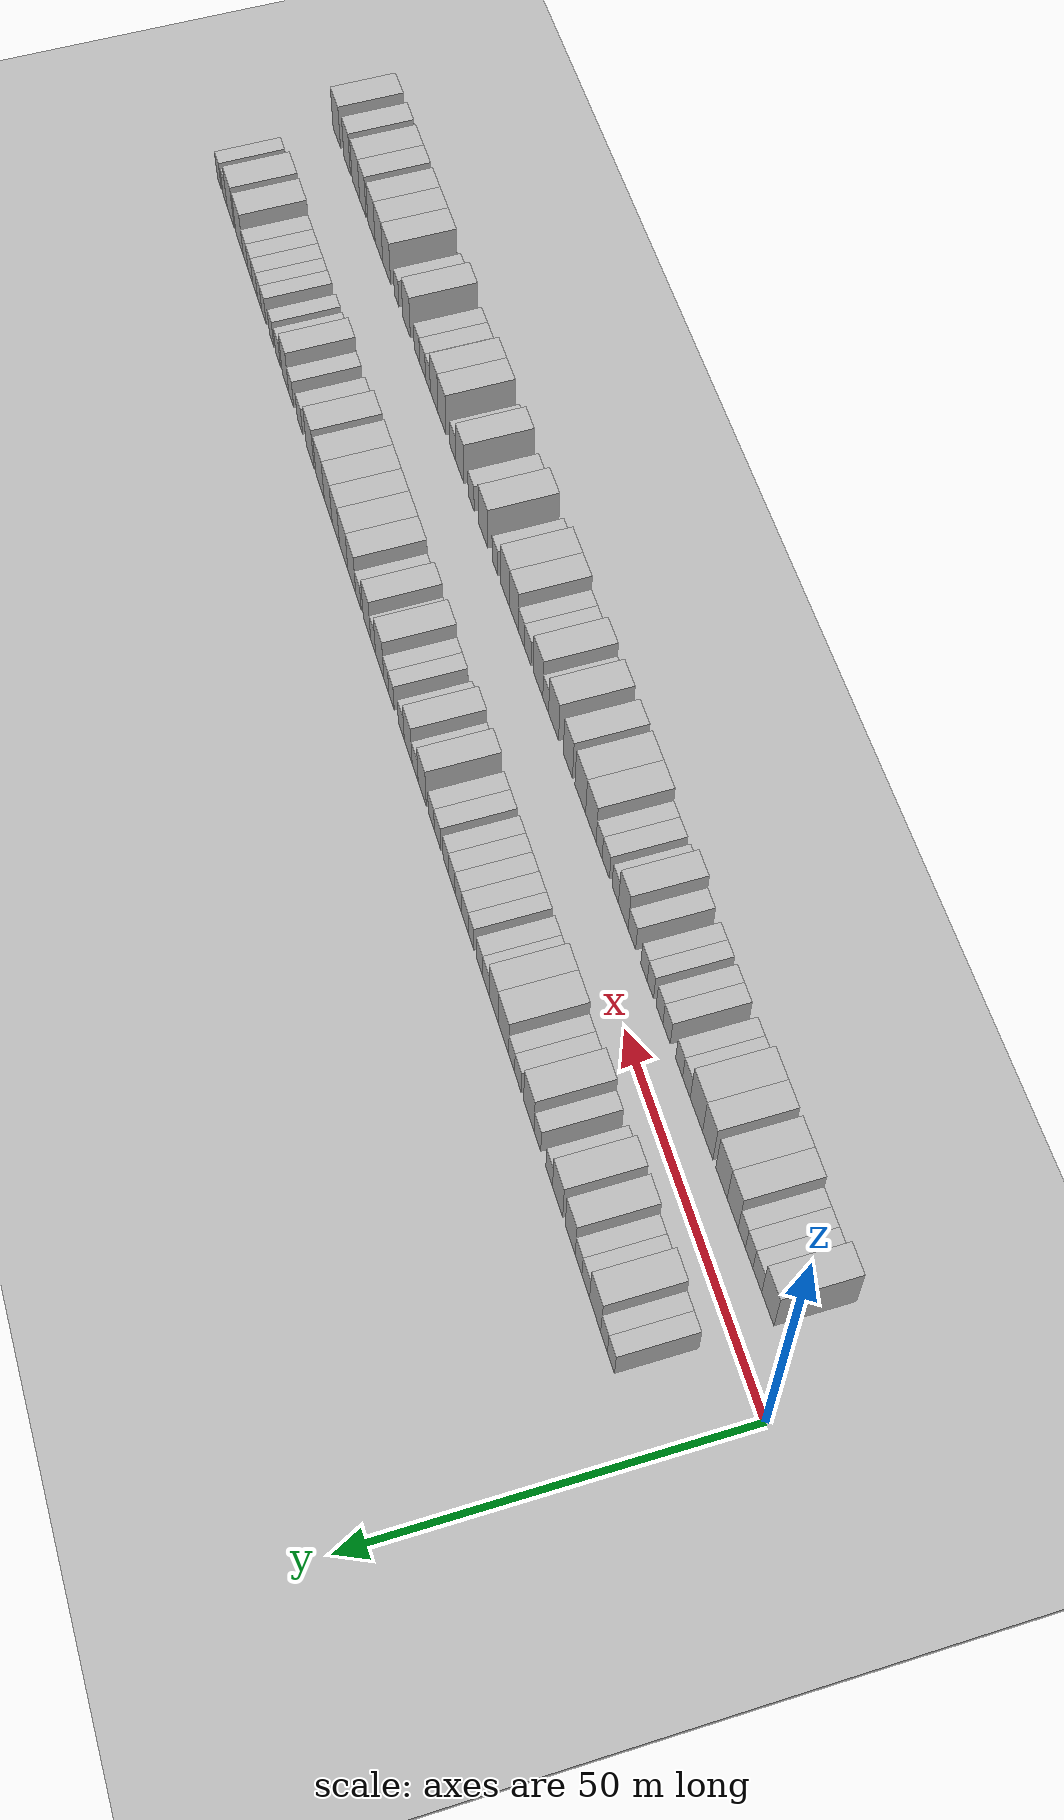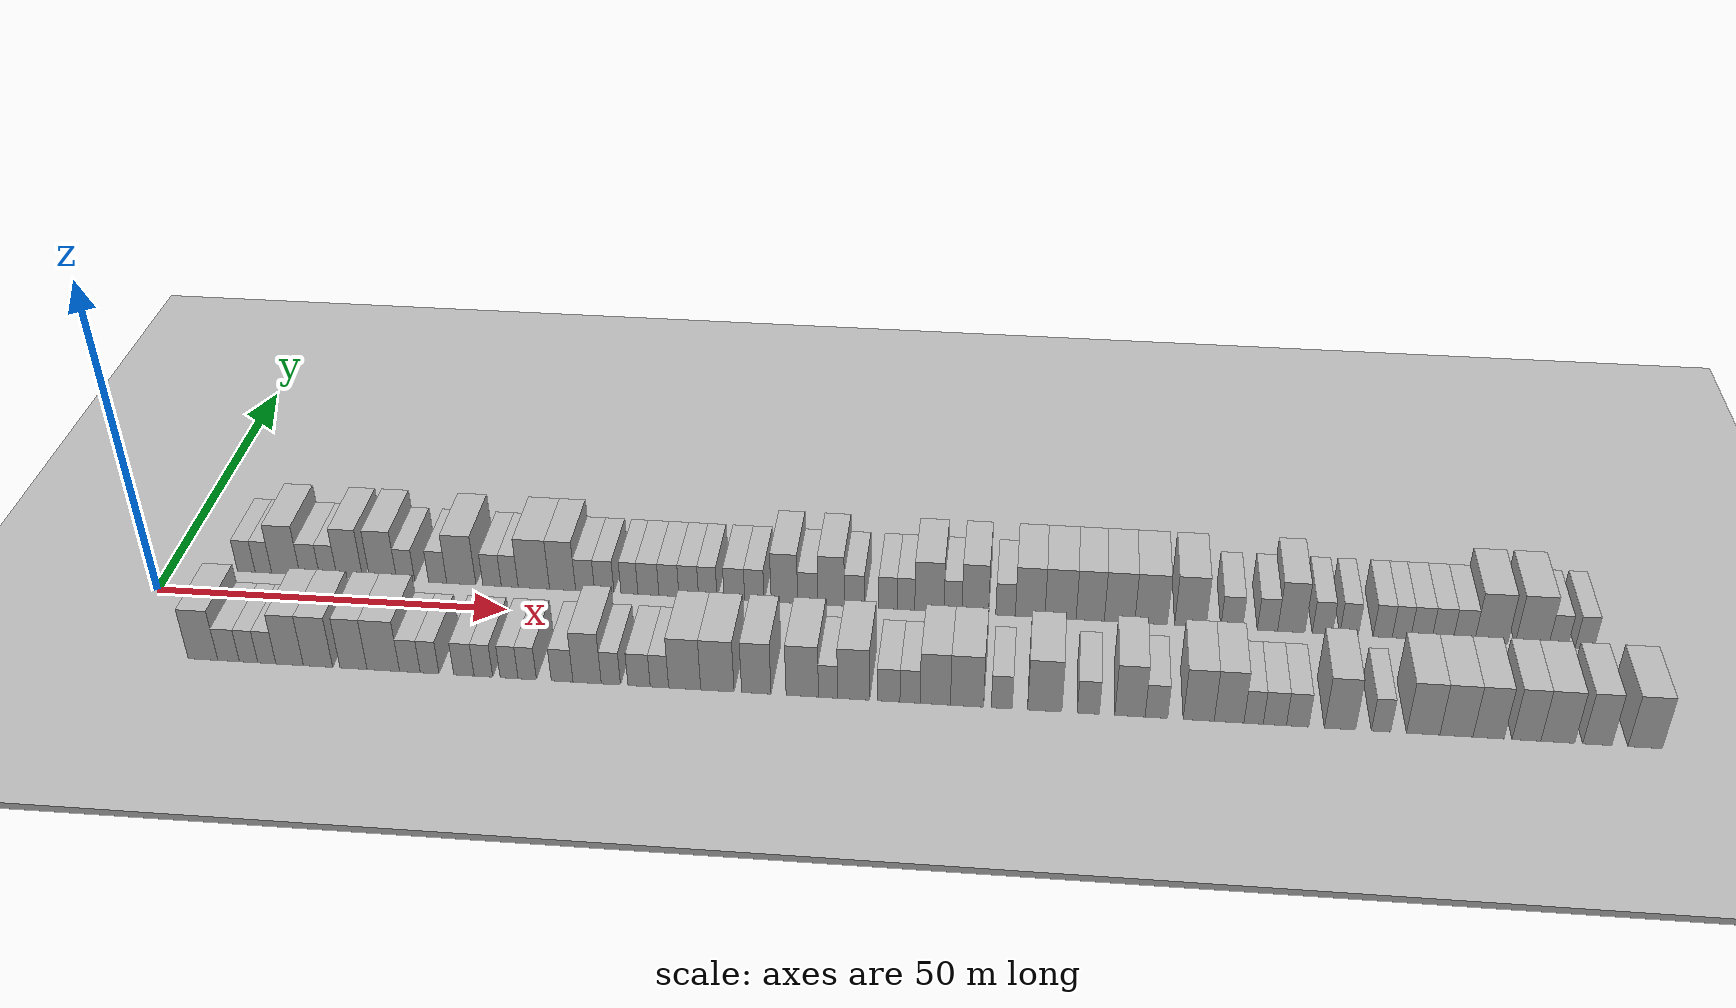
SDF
<?xml version="1.0" encoding="utf-8"?>

<sdf version="1.6">

   <world name="default">

      <gui fullscreen="0">

         <camera name="user_camera">

            <pose>-15 0 4.57585 0 0 0</pose>

            <view_controller>orbit</view_controller>

         </camera>

      </gui>

      <scene>

         <sky>

           <clouds>

             <speed>12</speed>

           </clouds>

         </sky>

         <ambient>0.4 0.4 0.4 1</ambient>

         <background>0.7 0.7 0.7 1</background>

         <shadows>1</shadows>

      </scene>

      <gravity>0 0 -9.8066</gravity>

      <magnetic_field>6e-06 2.3e-05 -4.2e-05</magnetic_field>

      <physics default="0" name="default_physics" type="ode">

         <ode>

            <solver>

               <type>quick</type>

               <iters>10</iters>

               <sor>1.0</sor>

               <use_dynamic_moi_rescaling>0</use_dynamic_moi_rescaling>

            </solver>

            <constraints>

               <cfm>0</cfm>

               <erp>0.2</erp>

               <contact_max_correcting_vel>100</contact_max_correcting_vel>

               <contact_surface_layer>0.001</contact_surface_layer>

            </constraints>

         </ode>

         <max_step_size>0.004</max_step_size>

         <real_time_factor>1</real_time_factor>

         <real_time_update_rate>250</real_time_update_rate>

      </physics>

      <light name="sun" type="directional">

         <cast_shadows>1</cast_shadows>

         <pose>0 0 10 0 0 0</pose>

         <diffuse>0.8 0.8 0.8 1</diffuse>

         <specular>0.2 0.2 0.2 1</specular>

         <attenuation>

            <range>1000</range>

            <constant>0.9</constant>

            <linear>0.01</linear>

            <quadratic>0.001</quadratic>

         </attenuation>

         <direction>-0.5 0.1 -0.9</direction>

      </light>

      <include>

         <name>ground_plane_1</name>

         <uri>model://HANNAS_ground_plane</uri>

         <pose>0 0 0  0 0 0</pose>

      </include>

      <include>

         <name>ground_plane_2</name>

         <uri>model://HANNAS_ground_plane</uri>

         <pose>100 0 0  0 0 0</pose>

      </include>

      <model name="building_1">

         <static>1</static>

         <pose frame="">11.2882 9.5000 0 0.000000 0.000000 1.570796</pose>

         <link name="link">

            <pose frame="">0 0 3.00 0 0 0</pose>

            <collision name="collision">

               <geometry>

                  <box>

                     <size>10.0000 2.5765 6.0000</size>

                  </box>

               </geometry>

               <max_contacts>10</max_contacts>

               <surface>

                  <contact>

                     <ode/>

                  </contact>

                  <bounce/>

                  <friction>

                     <torsional>

                        <ode/>

                     </torsional>

                     <ode/>

                  </friction>

               </surface>

            </collision>

            <visual name="visual">

               <cast_shadows>0</cast_shadows>

               <geometry>

                  <box>

                     <size>10.0000 2.5765 6.0000</size>

                  </box>

               </geometry>

               <material>

                  <script>

                     <uri>model://HANNAS_wall/materials/scripts</uri>

                     <uri>model://HANNAS_wall/materials/textures</uri>

                     <name>vrc/HANNAS_wall</name>

                  </script>

               </material>

            </visual>

            <self_collide>0</self_collide>

            <enable_wind>0</enable_wind>

            <kinematic>0</kinematic>

         </link>

      </model>

      <model name="building_2">

         <static>1</static>

         <pose frame="">13.7909 9.5000 0 0.000000 0.000000 1.570796</pose>

         <link name="link">

            <pose frame="">0 0 3.00 0 0 0</pose>

            <collision name="collision">

               <geometry>

                  <box>

                     <size>10.0000 2.4288 6.0000</size>

                  </box>

               </geometry>

               <max_contacts>10</max_contacts>

               <surface>

                  <contact>

                     <ode/>

                  </contact>

                  <bounce/>

                  <friction>

                     <torsional>

                        <ode/>

                     </torsional>

                     <ode/>

                  </friction>

               </surface>

            </collision>

            <visual name="visual">

               <cast_shadows>0</cast_shadows>

               <geometry>

                  <box>

                     <size>10.0000 2.4288 6.0000</size>

                  </box>

               </geometry>

               <material>

                  <script>

                     <uri>model://HANNAS_wall/materials/scripts</uri>

                     <uri>model://HANNAS_wall/materials/textures</uri>

                     <name>vrc/HANNAS_wall</name>

                  </script>

               </material>

            </visual>

            <self_collide>0</self_collide>

            <enable_wind>0</enable_wind>

            <kinematic>0</kinematic>

         </link>

      </model>

      <model name="building_3">

         <static>1</static>

         <pose frame="">17.0592 9.5000 0 0.000000 0.000000 1.570796</pose>

         <link name="link">

            <pose frame="">0 0 4.50 0 0 0</pose>

            <collision name="collision">

               <geometry>

                  <box>

                     <size>10.0000 4.1080 9.0000</size>

                  </box>

               </geometry>

               <max_contacts>10</max_contacts>

               <surface>

                  <contact>

                     <ode/>

                  </contact>

                  <bounce/>

                  <friction>

                     <torsional>

                        <ode/>

                     </torsional>

                     <ode/>

                  </friction>

               </surface>

            </collision>

            <visual name="visual">

               <cast_shadows>0</cast_shadows>

               <geometry>

                  <box>

                     <size>10.0000 4.1080 9.0000</size>

                  </box>

               </geometry>

               <material>

                  <script>

                     <uri>model://HANNAS_wall/materials/scripts</uri>

                     <uri>model://HANNAS_wall/materials/textures</uri>

                     <name>vrc/HANNAS_wall</name>

                  </script>

               </material>

            </visual>

            <self_collide>0</self_collide>

            <enable_wind>0</enable_wind>

            <kinematic>0</kinematic>

         </link>

      </model>

      <model name="building_4">

         <static>1</static>

         <pose frame="">20.5396 9.5000 0 0.000000 0.000000 1.570796</pose>

         <link name="link">

            <pose frame="">0 0 3.00 0 0 0</pose>

            <collision name="collision">

               <geometry>

                  <box>

                     <size>10.0000 2.8527 6.0000</size>

                  </box>

               </geometry>

               <max_contacts>10</max_contacts>

               <surface>

                  <contact>

                     <ode/>

                  </contact>

                  <bounce/>

                  <friction>

                     <torsional>

                        <ode/>

                     </torsional>

                     <ode/>

                  </friction>

               </surface>

            </collision>

            <visual name="visual">

               <cast_shadows>0</cast_shadows>

               <geometry>

                  <box>

                     <size>10.0000 2.8527 6.0000</size>

                  </box>

               </geometry>

               <material>

                  <script>

                     <uri>model://HANNAS_wall/materials/scripts</uri>

                     <uri>model://HANNAS_wall/materials/textures</uri>

                     <name>vrc/HANNAS_wall</name>

                  </script>

               </material>

            </visual>

            <self_collide>0</self_collide>

            <enable_wind>0</enable_wind>

            <kinematic>0</kinematic>

         </link>

      </model>

      <model name="building_5">

         <static>1</static>

         <pose frame="">23.2264 9.5000 0 0.000000 0.000000 1.570796</pose>

         <link name="link">

            <pose frame="">0 0 3.00 0 0 0</pose>

            <collision name="collision">

               <geometry>

                  <box>

                     <size>10.0000 2.5211 6.0000</size>

                  </box>

               </geometry>

               <max_contacts>10</max_contacts>

               <surface>

                  <contact>

                     <ode/>

                  </contact>

                  <bounce/>

                  <friction>

                     <torsional>

                        <ode/>

                     </torsional>

                     <ode/>

                  </friction>

               </surface>

            </collision>

            <visual name="visual">

               <cast_shadows>0</cast_shadows>

               <geometry>

                  <box>

                     <size>10.0000 2.5211 6.0000</size>

                  </box>

               </geometry>

               <material>

                  <script>

                     <uri>model://HANNAS_wall/materials/scripts</uri>

                     <uri>model://HANNAS_wall/materials/textures</uri>

                     <name>vrc/HANNAS_wall</name>

                  </script>

               </material>

            </visual>

            <self_collide>0</self_collide>

            <enable_wind>0</enable_wind>

            <kinematic>0</kinematic>

         </link>

      </model>

      <model name="building_6">

         <static>1</static>

         <pose frame="">26.3644 9.5000 0 0.000000 0.000000 1.570796</pose>

         <link name="link">

            <pose frame="">0 0 4.50 0 0 0</pose>

            <collision name="collision">

               <geometry>

                  <box>

                     <size>10.0000 3.7548 9.0000</size>

                  </box>

               </geometry>

               <max_contacts>10</max_contacts>

               <surface>

                  <contact>

                     <ode/>

                  </contact>

                  <bounce/>

                  <friction>

                     <torsional>

                        <ode/>

                     </torsional>

                     <ode/>

                  </friction>

               </surface>

            </collision>

            <visual name="visual">

               <cast_shadows>0</cast_shadows>

               <geometry>

                  <box>

                     <size>10.0000 3.7548 9.0000</size>

                  </box>

               </geometry>

               <material>

                  <script>

                     <uri>model://HANNAS_wall/materials/scripts</uri>

                     <uri>model://HANNAS_wall/materials/textures</uri>

                     <name>vrc/HANNAS_wall</name>

                  </script>

               </material>

            </visual>

            <self_collide>0</self_collide>

            <enable_wind>0</enable_wind>

            <kinematic>0</kinematic>

         </link>

      </model>

      <model name="building_7">

         <static>1</static>

         <pose frame="">31.1983 9.5000 0 0.000000 0.000000 1.570796</pose>

         <link name="link">

            <pose frame="">0 0 4.50 0 0 0</pose>

            <collision name="collision">

               <geometry>

                  <box>

                     <size>10.0000 3.9130 9.0000</size>

                  </box>

               </geometry>

               <max_contacts>10</max_contacts>

               <surface>

                  <contact>

                     <ode/>

                  </contact>

                  <bounce/>

                  <friction>

                     <torsional>

                        <ode/>

                     </torsional>

                     <ode/>

                  </friction>

               </surface>

            </collision>

            <visual name="visual">

               <cast_shadows>0</cast_shadows>

               <geometry>

                  <box>

                     <size>10.0000 3.9130 9.0000</size>

                  </box>

               </geometry>

               <material>

                  <script>

                     <uri>model://HANNAS_wall/materials/scripts</uri>

                     <uri>model://HANNAS_wall/materials/textures</uri>

                     <name>vrc/HANNAS_wall</name>

                  </script>

               </material>

            </visual>

            <self_collide>0</self_collide>

            <enable_wind>0</enable_wind>

            <kinematic>0</kinematic>

         </link>

      </model>

      <model name="building_8">

         <static>1</static>

         <pose frame="">34.4615 9.5000 0 0.000000 0.000000 1.570796</pose>

         <link name="link">

            <pose frame="">0 0 3.00 0 0 0</pose>

            <collision name="collision">

               <geometry>

                  <box>

                     <size>10.0000 2.6134 6.0000</size>

                  </box>

               </geometry>

               <max_contacts>10</max_contacts>

               <surface>

                  <contact>

                     <ode/>

                  </contact>

                  <bounce/>

                  <friction>

                     <torsional>

                        <ode/>

                     </torsional>

                     <ode/>

                  </friction>

               </surface>

            </collision>

            <visual name="visual">

               <cast_shadows>0</cast_shadows>

               <geometry>

                  <box>

                     <size>10.0000 2.6134 6.0000</size>

                  </box>

               </geometry>

               <material>

                  <script>

                     <uri>model://HANNAS_wall/materials/scripts</uri>

                     <uri>model://HANNAS_wall/materials/textures</uri>

                     <name>vrc/HANNAS_wall</name>

                  </script>

               </material>

            </visual>

            <self_collide>0</self_collide>

            <enable_wind>0</enable_wind>

            <kinematic>0</kinematic>

         </link>

      </model>

      <model name="building_9">

         <static>1</static>

         <pose frame="">39.0749 9.5000 0 0.000000 0.000000 1.570796</pose>

         <link name="link">

            <pose frame="">0 0 3.00 0 0 0</pose>

            <collision name="collision">

               <geometry>

                  <box>

                     <size>10.0000 2.6134 6.0000</size>

                  </box>

               </geometry>

               <max_contacts>10</max_contacts>

               <surface>

                  <contact>

                     <ode/>

                  </contact>

                  <bounce/>

                  <friction>

                     <torsional>

                        <ode/>

                     </torsional>

                     <ode/>

                  </friction>

               </surface>

            </collision>

            <visual name="visual">

               <cast_shadows>0</cast_shadows>

               <geometry>

                  <box>

                     <size>10.0000 2.6134 6.0000</size>

                  </box>

               </geometry>

               <material>

                  <script>

                     <uri>model://HANNAS_wall/materials/scripts</uri>

                     <uri>model://HANNAS_wall/materials/textures</uri>

                     <name>vrc/HANNAS_wall</name>

                  </script>

               </material>

            </visual>

            <self_collide>0</self_collide>

            <enable_wind>0</enable_wind>

            <kinematic>0</kinematic>

         </link>

      </model>

      <model name="building_10">

         <static>1</static>

         <pose frame="">42.4751 9.5000 0 0.000000 0.000000 1.570796</pose>

         <link name="link">

            <pose frame="">0 0 4.50 0 0 0</pose>

            <collision name="collision">

               <geometry>

                  <box>

                     <size>10.0000 4.1871 9.0000</size>

                  </box>

               </geometry>

               <max_contacts>10</max_contacts>

               <surface>

                  <contact>

                     <ode/>

                  </contact>

                  <bounce/>

                  <friction>

                     <torsional>

                        <ode/>

                     </torsional>

                     <ode/>

                  </friction>

               </surface>

            </collision>

            <visual name="visual">

               <cast_shadows>0</cast_shadows>

               <geometry>

                  <box>

                     <size>10.0000 4.1871 9.0000</size>

                  </box>

               </geometry>

               <material>

                  <script>

                     <uri>model://HANNAS_wall/materials/scripts</uri>

                     <uri>model://HANNAS_wall/materials/textures</uri>

                     <name>vrc/HANNAS_wall</name>

                  </script>

               </material>

            </visual>

            <self_collide>0</self_collide>

            <enable_wind>0</enable_wind>

            <kinematic>0</kinematic>

         </link>

      </model>

      <model name="building_11">

         <static>1</static>

         <pose frame="">46.8850 9.5000 0 0.000000 0.000000 1.570796</pose>

         <link name="link">

            <pose frame="">0 0 3.00 0 0 0</pose>

            <collision name="collision">

               <geometry>

                  <box>

                     <size>10.0000 2.6326 6.0000</size>

                  </box>

               </geometry>

               <max_contacts>10</max_contacts>

               <surface>

                  <contact>

                     <ode/>

                  </contact>

                  <bounce/>

                  <friction>

                     <torsional>

                        <ode/>

                     </torsional>

                     <ode/>

                  </friction>

               </surface>

            </collision>

            <visual name="visual">

               <cast_shadows>0</cast_shadows>

               <geometry>

                  <box>

                     <size>10.0000 2.6326 6.0000</size>

                  </box>

               </geometry>

               <material>

                  <script>

                     <uri>model://HANNAS_wall/materials/scripts</uri>

                     <uri>model://HANNAS_wall/materials/textures</uri>

                     <name>vrc/HANNAS_wall</name>

                  </script>

               </material>

            </visual>

            <self_collide>0</self_collide>

            <enable_wind>0</enable_wind>

            <kinematic>0</kinematic>

         </link>

      </model>

      <model name="building_12">

         <static>1</static>

         <pose frame="">49.4207 9.5000 0 0.000000 0.000000 1.570796</pose>

         <link name="link">

            <pose frame="">0 0 3.00 0 0 0</pose>

            <collision name="collision">

               <geometry>

                  <box>

                     <size>10.0000 2.4388 6.0000</size>

                  </box>

               </geometry>

               <max_contacts>10</max_contacts>

               <surface>

                  <contact>

                     <ode/>

                  </contact>

                  <bounce/>

                  <friction>

                     <torsional>

                        <ode/>

                     </torsional>

                     <ode/>

                  </friction>

               </surface>

            </collision>

            <visual name="visual">

               <cast_shadows>0</cast_shadows>

               <geometry>

                  <box>

                     <size>10.0000 2.4388 6.0000</size>

                  </box>

               </geometry>

               <material>

                  <script>

                     <uri>model://HANNAS_wall/materials/scripts</uri>

                     <uri>model://HANNAS_wall/materials/textures</uri>

                     <name>vrc/HANNAS_wall</name>

                  </script>

               </material>

            </visual>

            <self_collide>0</self_collide>

            <enable_wind>0</enable_wind>

            <kinematic>0</kinematic>

         </link>

      </model>

      <model name="building_13">

         <static>1</static>

         <pose frame="">52.8807 9.5000 0 0.000000 0.000000 1.570796</pose>

         <link name="link">

            <pose frame="">0 0 4.50 0 0 0</pose>

            <collision name="collision">

               <geometry>

                  <box>

                     <size>10.0000 4.4811 9.0000</size>

                  </box>

               </geometry>

               <max_contacts>10</max_contacts>

               <surface>

                  <contact>

                     <ode/>

                  </contact>

                  <bounce/>

                  <friction>

                     <torsional>

                        <ode/>

                     </torsional>

                     <ode/>

                  </friction>

               </surface>

            </collision>

            <visual name="visual">

               <cast_shadows>0</cast_shadows>

               <geometry>

                  <box>

                     <size>10.0000 4.4811 9.0000</size>

                  </box>

               </geometry>

               <material>

                  <script>

                     <uri>model://HANNAS_wall/materials/scripts</uri>

                     <uri>model://HANNAS_wall/materials/textures</uri>

                     <name>vrc/HANNAS_wall</name>

                  </script>

               </material>

            </visual>

            <self_collide>0</self_collide>

            <enable_wind>0</enable_wind>

            <kinematic>0</kinematic>

         </link>

      </model>

      <model name="building_14">

         <static>1</static>

         <pose frame="">56.9827 9.5000 0 0.000000 0.000000 1.570796</pose>

         <link name="link">

            <pose frame="">0 0 4.50 0 0 0</pose>

            <collision name="collision">

               <geometry>

                  <box>

                     <size>10.0000 3.7229 9.0000</size>

                  </box>

               </geometry>

               <max_contacts>10</max_contacts>

               <surface>

                  <contact>

                     <ode/>

                  </contact>

                  <bounce/>

                  <friction>

                     <torsional>

                        <ode/>

                     </torsional>

                     <ode/>

                  </friction>

               </surface>

            </collision>

            <visual name="visual">

               <cast_shadows>0</cast_shadows>

               <geometry>

                  <box>

                     <size>10.0000 3.7229 9.0000</size>

                  </box>

               </geometry>

               <material>

                  <script>

                     <uri>model://HANNAS_wall/materials/scripts</uri>

                     <uri>model://HANNAS_wall/materials/textures</uri>

                     <name>vrc/HANNAS_wall</name>

                  </script>

               </material>

            </visual>

            <self_collide>0</self_collide>

            <enable_wind>0</enable_wind>

            <kinematic>0</kinematic>

         </link>

      </model>

      <model name="building_15">

         <static>1</static>

         <pose frame="">60.1953 9.5000 0 0.000000 0.000000 1.570796</pose>

         <link name="link">

            <pose frame="">0 0 3.00 0 0 0</pose>

            <collision name="collision">

               <geometry>

                  <box>

                     <size>10.0000 2.7024 6.0000</size>

                  </box>

               </geometry>

               <max_contacts>10</max_contacts>

               <surface>

                  <contact>

                     <ode/>

                  </contact>

                  <bounce/>

                  <friction>

                     <torsional>

                        <ode/>

                     </torsional>

                     <ode/>

                  </friction>

               </surface>

            </collision>

            <visual name="visual">

               <cast_shadows>0</cast_shadows>

               <geometry>

                  <box>

                     <size>10.0000 2.7024 6.0000</size>

                  </box>

               </geometry>

               <material>

                  <script>

                     <uri>model://HANNAS_wall/materials/scripts</uri>

                     <uri>model://HANNAS_wall/materials/textures</uri>

                     <name>vrc/HANNAS_wall</name>

                  </script>

               </material>

            </visual>

            <self_collide>0</self_collide>

            <enable_wind>0</enable_wind>

            <kinematic>0</kinematic>

         </link>

      </model>

      <model name="building_16">

         <static>1</static>

         <pose frame="">62.9244 9.5000 0 0.000000 0.000000 1.570796</pose>

         <link name="link">

            <pose frame="">0 0 3.00 0 0 0</pose>

            <collision name="collision">

               <geometry>

                  <box>

                     <size>10.0000 2.7558 6.0000</size>

                  </box>

               </geometry>

               <max_contacts>10</max_contacts>

               <surface>

                  <contact>

                     <ode/>

                  </contact>

                  <bounce/>

                  <friction>

                     <torsional>

                        <ode/>

                     </torsional>

                     <ode/>

                  </friction>

               </surface>

            </collision>

            <visual name="visual">

               <cast_shadows>0</cast_shadows>

               <geometry>

                  <box>

                     <size>10.0000 2.7558 6.0000</size>

                  </box>

               </geometry>

               <material>

                  <script>

                     <uri>model://HANNAS_wall/materials/scripts</uri>

                     <uri>model://HANNAS_wall/materials/textures</uri>

                     <name>vrc/HANNAS_wall</name>

                  </script>

               </material>

            </visual>

            <self_collide>0</self_collide>

            <enable_wind>0</enable_wind>

            <kinematic>0</kinematic>

         </link>

      </model>

      <model name="building_17">

         <static>1</static>

         <pose frame="">66.5044 9.5000 0 0.000000 0.000000 1.570796</pose>

         <link name="link">

            <pose frame="">0 0 3.00 0 0 0</pose>

            <collision name="collision">

               <geometry>

                  <box>

                     <size>10.0000 2.4043 6.0000</size>

                  </box>

               </geometry>

               <max_contacts>10</max_contacts>

               <surface>

                  <contact>

                     <ode/>

                  </contact>

                  <bounce/>

                  <friction>

                     <torsional>

                        <ode/>

                     </torsional>

                     <ode/>

                  </friction>

               </surface>

            </collision>

            <visual name="visual">

               <cast_shadows>0</cast_shadows>

               <geometry>

                  <box>

                     <size>10.0000 2.4043 6.0000</size>

                  </box>

               </geometry>

               <material>

                  <script>

                     <uri>model://HANNAS_wall/materials/scripts</uri>

                     <uri>model://HANNAS_wall/materials/textures</uri>

                     <name>vrc/HANNAS_wall</name>

                  </script>

               </material>

            </visual>

            <self_collide>0</self_collide>

            <enable_wind>0</enable_wind>

            <kinematic>0</kinematic>

         </link>

      </model>

      <model name="building_18">

         <static>1</static>

         <pose frame="">69.1993 9.5000 0 0.000000 0.000000 1.570796</pose>

         <link name="link">

            <pose frame="">0 0 3.00 0 0 0</pose>

            <collision name="collision">

               <geometry>

                  <box>

                     <size>10.0000 2.9854 6.0000</size>

                  </box>

               </geometry>

               <max_contacts>10</max_contacts>

               <surface>

                  <contact>

                     <ode/>

                  </contact>

                  <bounce/>

                  <friction>

                     <torsional>

                        <ode/>

                     </torsional>

                     <ode/>

                  </friction>

               </surface>

            </collision>

            <visual name="visual">

               <cast_shadows>0</cast_shadows>

               <geometry>

                  <box>

                     <size>10.0000 2.9854 6.0000</size>

                  </box>

               </geometry>

               <material>

                  <script>

                     <uri>model://HANNAS_wall/materials/scripts</uri>

                     <uri>model://HANNAS_wall/materials/textures</uri>

                     <name>vrc/HANNAS_wall</name>

                  </script>

               </material>

            </visual>

            <self_collide>0</self_collide>

            <enable_wind>0</enable_wind>

            <kinematic>0</kinematic>

         </link>

      </model>

      <model name="building_19">

         <static>1</static>

         <pose frame="">72.1082 9.5000 0 0.000000 0.000000 1.570796</pose>

         <link name="link">

            <pose frame="">0 0 3.00 0 0 0</pose>

            <collision name="collision">

               <geometry>

                  <box>

                     <size>10.0000 2.8324 6.0000</size>

                  </box>

               </geometry>

               <max_contacts>10</max_contacts>

               <surface>

                  <contact>

                     <ode/>

                  </contact>

                  <bounce/>

                  <friction>

                     <torsional>

                        <ode/>

                     </torsional>

                     <ode/>

                  </friction>

               </surface>

            </collision>

            <visual name="visual">

               <cast_shadows>0</cast_shadows>

               <geometry>

                  <box>

                     <size>10.0000 2.8324 6.0000</size>

                  </box>

               </geometry>

               <material>

                  <script>

                     <uri>model://HANNAS_wall/materials/scripts</uri>

                     <uri>model://HANNAS_wall/materials/textures</uri>

                     <name>vrc/HANNAS_wall</name>

                  </script>

               </material>

            </visual>

            <self_collide>0</self_collide>

            <enable_wind>0</enable_wind>

            <kinematic>0</kinematic>

         </link>

      </model>

      <model name="building_20">

         <static>1</static>

         <pose frame="">74.9135 9.5000 0 0.000000 0.000000 1.570796</pose>

         <link name="link">

            <pose frame="">0 0 3.00 0 0 0</pose>

            <collision name="collision">

               <geometry>

                  <box>

                     <size>10.0000 2.7782 6.0000</size>

                  </box>

               </geometry>

               <max_contacts>10</max_contacts>

               <surface>

                  <contact>

                     <ode/>

                  </contact>

                  <bounce/>

                  <friction>

                     <torsional>

                        <ode/>

                     </torsional>

                     <ode/>

                  </friction>

               </surface>

            </collision>

            <visual name="visual">

               <cast_shadows>0</cast_shadows>

               <geometry>

                  <box>

                     <size>10.0000 2.7782 6.0000</size>

                  </box>

               </geometry>

               <material>

                  <script>

                     <uri>model://HANNAS_wall/materials/scripts</uri>

                     <uri>model://HANNAS_wall/materials/textures</uri>

                     <name>vrc/HANNAS_wall</name>

                  </script>

               </material>

            </visual>

            <self_collide>0</self_collide>

            <enable_wind>0</enable_wind>

            <kinematic>0</kinematic>

         </link>

      </model>

      <model name="building_21">

         <static>1</static>

         <pose frame="">77.6071 9.5000 0 0.000000 0.000000 1.570796</pose>

         <link name="link">

            <pose frame="">0 0 3.00 0 0 0</pose>

            <collision name="collision">

               <geometry>

                  <box>

                     <size>10.0000 2.6091 6.0000</size>

                  </box>

               </geometry>

               <max_contacts>10</max_contacts>

               <surface>

                  <contact>

                     <ode/>

                  </contact>

                  <bounce/>

                  <friction>

                     <torsional>

                        <ode/>

                     </torsional>

                     <ode/>

                  </friction>

               </surface>

            </collision>

            <visual name="visual">

               <cast_shadows>0</cast_shadows>

               <geometry>

                  <box>

                     <size>10.0000 2.6091 6.0000</size>

                  </box>

               </geometry>

               <material>

                  <script>

                     <uri>model://HANNAS_wall/materials/scripts</uri>

                     <uri>model://HANNAS_wall/materials/textures</uri>

                     <name>vrc/HANNAS_wall</name>

                  </script>

               </material>

            </visual>

            <self_collide>0</self_collide>

            <enable_wind>0</enable_wind>

            <kinematic>0</kinematic>

         </link>

      </model>

      <model name="building_22">

         <static>1</static>

         <pose frame="">81.3599 9.5000 0 0.000000 0.000000 1.570796</pose>

         <link name="link">

            <pose frame="">0 0 3.00 0 0 0</pose>

            <collision name="collision">

               <geometry>

                  <box>

                     <size>10.0000 2.8966 6.0000</size>

                  </box>

               </geometry>

               <max_contacts>10</max_contacts>

               <surface>

                  <contact>

                     <ode/>

                  </contact>

                  <bounce/>

                  <friction>

                     <torsional>

                        <ode/>

                     </torsional>

                     <ode/>

                  </friction>

               </surface>

            </collision>

            <visual name="visual">

               <cast_shadows>0</cast_shadows>

               <geometry>

                  <box>

                     <size>10.0000 2.8966 6.0000</size>

                  </box>

               </geometry>

               <material>

                  <script>

                     <uri>model://HANNAS_wall/materials/scripts</uri>

                     <uri>model://HANNAS_wall/materials/textures</uri>

                     <name>vrc/HANNAS_wall</name>

                  </script>

               </material>

            </visual>

            <self_collide>0</self_collide>

            <enable_wind>0</enable_wind>

            <kinematic>0</kinematic>

         </link>

      </model>

      <model name="building_23">

         <static>1</static>

         <pose frame="">84.1726 9.5000 0 0.000000 0.000000 1.570796</pose>

         <link name="link">

            <pose frame="">0 0 3.00 0 0 0</pose>

            <collision name="collision">

               <geometry>

                  <box>

                     <size>10.0000 2.7287 6.0000</size>

                  </box>

               </geometry>

               <max_contacts>10</max_contacts>

               <surface>

                  <contact>

                     <ode/>

                  </contact>

                  <bounce/>

                  <friction>

                     <torsional>

                        <ode/>

                     </torsional>

                     <ode/>

                  </friction>

               </surface>

            </collision>

            <visual name="visual">

               <cast_shadows>0</cast_shadows>

               <geometry>

                  <box>

                     <size>10.0000 2.7287 6.0000</size>

                  </box>

               </geometry>

               <material>

                  <script>

                     <uri>model://HANNAS_wall/materials/scripts</uri>

                     <uri>model://HANNAS_wall/materials/textures</uri>

                     <name>vrc/HANNAS_wall</name>

                  </script>

               </material>

            </visual>

            <self_collide>0</self_collide>

            <enable_wind>0</enable_wind>

            <kinematic>0</kinematic>

         </link>

      </model>

      <model name="building_24">

         <static>1</static>

         <pose frame="">88.4007 9.5000 0 0.000000 0.000000 1.570796</pose>

         <link name="link">

            <pose frame="">0 0 4.50 0 0 0</pose>

            <collision name="collision">

               <geometry>

                  <box>

                     <size>10.0000 3.7275 9.0000</size>

                  </box>

               </geometry>

               <max_contacts>10</max_contacts>

               <surface>

                  <contact>

                     <ode/>

                  </contact>

                  <bounce/>

                  <friction>

                     <torsional>

                        <ode/>

                     </torsional>

                     <ode/>

                  </friction>

               </surface>

            </collision>

            <visual name="visual">

               <cast_shadows>0</cast_shadows>

               <geometry>

                  <box>

                     <size>10.0000 3.7275 9.0000</size>

                  </box>

               </geometry>

               <material>

                  <script>

                     <uri>model://HANNAS_wall/materials/scripts</uri>

                     <uri>model://HANNAS_wall/materials/textures</uri>

                     <name>vrc/HANNAS_wall</name>

                  </script>

               </material>

            </visual>

            <self_collide>0</self_collide>

            <enable_wind>0</enable_wind>

            <kinematic>0</kinematic>

         </link>

      </model>

      <model name="building_25">

         <static>1</static>

         <pose frame="">91.6844 9.5000 0 0.000000 0.000000 1.570796</pose>

         <link name="link">

            <pose frame="">0 0 3.00 0 0 0</pose>

            <collision name="collision">

               <geometry>

                  <box>

                     <size>10.0000 2.8400 6.0000</size>

                  </box>

               </geometry>

               <max_contacts>10</max_contacts>

               <surface>

                  <contact>

                     <ode/>

                  </contact>

                  <bounce/>

                  <friction>

                     <torsional>

                        <ode/>

                     </torsional>

                     <ode/>

                  </friction>

               </surface>

            </collision>

            <visual name="visual">

               <cast_shadows>0</cast_shadows>

               <geometry>

                  <box>

                     <size>10.0000 2.8400 6.0000</size>

                  </box>

               </geometry>

               <material>

                  <script>

                     <uri>model://HANNAS_wall/materials/scripts</uri>

                     <uri>model://HANNAS_wall/materials/textures</uri>

                     <name>vrc/HANNAS_wall</name>

                  </script>

               </material>

            </visual>

            <self_collide>0</self_collide>

            <enable_wind>0</enable_wind>

            <kinematic>0</kinematic>

         </link>

      </model>

      <model name="building_26">

         <static>1</static>

         <pose frame="">94.9504 9.5000 0 0.000000 0.000000 1.570796</pose>

         <link name="link">

            <pose frame="">0 0 4.50 0 0 0</pose>

            <collision name="collision">

               <geometry>

                  <box>

                     <size>10.0000 3.6920 9.0000</size>

                  </box>

               </geometry>

               <max_contacts>10</max_contacts>

               <surface>

                  <contact>

                     <ode/>

                  </contact>

                  <bounce/>

                  <friction>

                     <torsional>

                        <ode/>

                     </torsional>

                     <ode/>

                  </friction>

               </surface>

            </collision>

            <visual name="visual">

               <cast_shadows>0</cast_shadows>

               <geometry>

                  <box>

                     <size>10.0000 3.6920 9.0000</size>

                  </box>

               </geometry>

               <material>

                  <script>

                     <uri>model://HANNAS_wall/materials/scripts</uri>

                     <uri>model://HANNAS_wall/materials/textures</uri>

                     <name>vrc/HANNAS_wall</name>

                  </script>

               </material>

            </visual>

            <self_collide>0</self_collide>

            <enable_wind>0</enable_wind>

            <kinematic>0</kinematic>

         </link>

      </model>

      <model name="building_27">

         <static>1</static>

         <pose frame="">98.1973 9.5000 0 0.000000 0.000000 1.570796</pose>

         <link name="link">

            <pose frame="">0 0 3.00 0 0 0</pose>

            <collision name="collision">

               <geometry>

                  <box>

                     <size>10.0000 2.8018 6.0000</size>

                  </box>

               </geometry>

               <max_contacts>10</max_contacts>

               <surface>

                  <contact>

                     <ode/>

                  </contact>

                  <bounce/>

                  <friction>

                     <torsional>

                        <ode/>

                     </torsional>

                     <ode/>

                  </friction>

               </surface>

            </collision>

            <visual name="visual">

               <cast_shadows>0</cast_shadows>

               <geometry>

                  <box>

                     <size>10.0000 2.8018 6.0000</size>

                  </box>

               </geometry>

               <material>

                  <script>

                     <uri>model://HANNAS_wall/materials/scripts</uri>

                     <uri>model://HANNAS_wall/materials/textures</uri>

                     <name>vrc/HANNAS_wall</name>

                  </script>

               </material>

            </visual>

            <self_collide>0</self_collide>

            <enable_wind>0</enable_wind>

            <kinematic>0</kinematic>

         </link>

      </model>

      <model name="building_28">

         <static>1</static>

         <pose frame="">102.8704 9.5000 0 0.000000 0.000000 1.570796</pose>

         <link name="link">

            <pose frame="">0 0 3.00 0 0 0</pose>

            <collision name="collision">

               <geometry>

                  <box>

                     <size>10.0000 2.5444 6.0000</size>

                  </box>

               </geometry>

               <max_contacts>10</max_contacts>

               <surface>

                  <contact>

                     <ode/>

                  </contact>

                  <bounce/>

                  <friction>

                     <torsional>

                        <ode/>

                     </torsional>

                     <ode/>

                  </friction>

               </surface>

            </collision>

            <visual name="visual">

               <cast_shadows>0</cast_shadows>

               <geometry>

                  <box>

                     <size>10.0000 2.5444 6.0000</size>

                  </box>

               </geometry>

               <material>

                  <script>

                     <uri>model://HANNAS_wall/materials/scripts</uri>

                     <uri>model://HANNAS_wall/materials/textures</uri>

                     <name>vrc/HANNAS_wall</name>

                  </script>

               </material>

            </visual>

            <self_collide>0</self_collide>

            <enable_wind>0</enable_wind>

            <kinematic>0</kinematic>

         </link>

      </model>

      <model name="building_29">

         <static>1</static>

         <pose frame="">105.3712 9.5000 0 0.000000 0.000000 1.570796</pose>

         <link name="link">

            <pose frame="">0 0 3.00 0 0 0</pose>

            <collision name="collision">

               <geometry>

                  <box>

                     <size>10.0000 2.4571 6.0000</size>

                  </box>

               </geometry>

               <max_contacts>10</max_contacts>

               <surface>

                  <contact>

                     <ode/>

                  </contact>

                  <bounce/>

                  <friction>

                     <torsional>

                        <ode/>

                     </torsional>

                     <ode/>

                  </friction>

               </surface>

            </collision>

            <visual name="visual">

               <cast_shadows>0</cast_shadows>

               <geometry>

                  <box>

                     <size>10.0000 2.4571 6.0000</size>

                  </box>

               </geometry>

               <material>

                  <script>

                     <uri>model://HANNAS_wall/materials/scripts</uri>

                     <uri>model://HANNAS_wall/materials/textures</uri>

                     <name>vrc/HANNAS_wall</name>

                  </script>

               </material>

            </visual>

            <self_collide>0</self_collide>

            <enable_wind>0</enable_wind>

            <kinematic>0</kinematic>

         </link>

      </model>

      <model name="building_30">

         <static>1</static>

         <pose frame="">108.6389 9.5000 0 0.000000 0.000000 1.570796</pose>

         <link name="link">

            <pose frame="">0 0 4.50 0 0 0</pose>

            <collision name="collision">

               <geometry>

                  <box>

                     <size>10.0000 4.0783 9.0000</size>

                  </box>

               </geometry>

               <max_contacts>10</max_contacts>

               <surface>

                  <contact>

                     <ode/>

                  </contact>

                  <bounce/>

                  <friction>

                     <torsional>

                        <ode/>

                     </torsional>

                     <ode/>

                  </friction>

               </surface>

            </collision>

            <visual name="visual">

               <cast_shadows>0</cast_shadows>

               <geometry>

                  <box>

                     <size>10.0000 4.0783 9.0000</size>

                  </box>

               </geometry>

               <material>

                  <script>

                     <uri>model://HANNAS_wall/materials/scripts</uri>

                     <uri>model://HANNAS_wall/materials/textures</uri>

                     <name>vrc/HANNAS_wall</name>

                  </script>

               </material>

            </visual>

            <self_collide>0</self_collide>

            <enable_wind>0</enable_wind>

            <kinematic>0</kinematic>

         </link>

      </model>

      <model name="building_31">

         <static>1</static>

         <pose frame="">111.9144 9.5000 0 0.000000 0.000000 1.570796</pose>

         <link name="link">

            <pose frame="">0 0 3.00 0 0 0</pose>

            <collision name="collision">

               <geometry>

                  <box>

                     <size>10.0000 2.4729 6.0000</size>

                  </box>

               </geometry>

               <max_contacts>10</max_contacts>

               <surface>

                  <contact>

                     <ode/>

                  </contact>

                  <bounce/>

                  <friction>

                     <torsional>

                        <ode/>

                     </torsional>

                     <ode/>

                  </friction>

               </surface>

            </collision>

            <visual name="visual">

               <cast_shadows>0</cast_shadows>

               <geometry>

                  <box>

                     <size>10.0000 2.4729 6.0000</size>

                  </box>

               </geometry>

               <material>

                  <script>

                     <uri>model://HANNAS_wall/materials/scripts</uri>

                     <uri>model://HANNAS_wall/materials/textures</uri>

                     <name>vrc/HANNAS_wall</name>

                  </script>

               </material>

            </visual>

            <self_collide>0</self_collide>

            <enable_wind>0</enable_wind>

            <kinematic>0</kinematic>

         </link>

      </model>

      <model name="building_32">

         <static>1</static>

         <pose frame="">114.9888 9.5000 0 0.000000 0.000000 1.570796</pose>

         <link name="link">

            <pose frame="">0 0 4.50 0 0 0</pose>

            <collision name="collision">

               <geometry>

                  <box>

                     <size>10.0000 3.6758 9.0000</size>

                  </box>

               </geometry>

               <max_contacts>10</max_contacts>

               <surface>

                  <contact>

                     <ode/>

                  </contact>

                  <bounce/>

                  <friction>

                     <torsional>

                        <ode/>

                     </torsional>

                     <ode/>

                  </friction>

               </surface>

            </collision>

            <visual name="visual">

               <cast_shadows>0</cast_shadows>

               <geometry>

                  <box>

                     <size>10.0000 3.6758 9.0000</size>

                  </box>

               </geometry>

               <material>

                  <script>

                     <uri>model://HANNAS_wall/materials/scripts</uri>

                     <uri>model://HANNAS_wall/materials/textures</uri>

                     <name>vrc/HANNAS_wall</name>

                  </script>

               </material>

            </visual>

            <self_collide>0</self_collide>

            <enable_wind>0</enable_wind>

            <kinematic>0</kinematic>

         </link>

      </model>

      <model name="building_33">

         <static>1</static>

         <pose frame="">119.1749 9.5000 0 0.000000 0.000000 1.570796</pose>

         <link name="link">

            <pose frame="">0 0 3.00 0 0 0</pose>

            <collision name="collision">

               <geometry>

                  <box>

                     <size>10.0000 2.6965 6.0000</size>

                  </box>

               </geometry>

               <max_contacts>10</max_contacts>

               <surface>

                  <contact>

                     <ode/>

                  </contact>

                  <bounce/>

                  <friction>

                     <torsional>

                        <ode/>

                     </torsional>

                     <ode/>

                  </friction>

               </surface>

            </collision>

            <visual name="visual">

               <cast_shadows>0</cast_shadows>

               <geometry>

                  <box>

                     <size>10.0000 2.6965 6.0000</size>

                  </box>

               </geometry>

               <material>

                  <script>

                     <uri>model://HANNAS_wall/materials/scripts</uri>

                     <uri>model://HANNAS_wall/materials/textures</uri>

                     <name>vrc/HANNAS_wall</name>

                  </script>

               </material>

            </visual>

            <self_collide>0</self_collide>

            <enable_wind>0</enable_wind>

            <kinematic>0</kinematic>

         </link>

      </model>

      <model name="building_34">

         <static>1</static>

         <pose frame="">122.5551 9.5000 0 0.000000 0.000000 1.570796</pose>

         <link name="link">

            <pose frame="">0 0 4.50 0 0 0</pose>

            <collision name="collision">

               <geometry>

                  <box>

                     <size>10.0000 4.0638 9.0000</size>

                  </box>

               </geometry>

               <max_contacts>10</max_contacts>

               <surface>

                  <contact>

                     <ode/>

                  </contact>

                  <bounce/>

                  <friction>

                     <torsional>

                        <ode/>

                     </torsional>

                     <ode/>

                  </friction>

               </surface>

            </collision>

            <visual name="visual">

               <cast_shadows>0</cast_shadows>

               <geometry>

                  <box>

                     <size>10.0000 4.0638 9.0000</size>

                  </box>

               </geometry>

               <material>

                  <script>

                     <uri>model://HANNAS_wall/materials/scripts</uri>

                     <uri>model://HANNAS_wall/materials/textures</uri>

                     <name>vrc/HANNAS_wall</name>

                  </script>

               </material>

            </visual>

            <self_collide>0</self_collide>

            <enable_wind>0</enable_wind>

            <kinematic>0</kinematic>

         </link>

      </model>

      <model name="building_35">

         <static>1</static>

         <pose frame="">126.7387 9.5000 0 0.000000 0.000000 1.570796</pose>

         <link name="link">

            <pose frame="">0 0 4.50 0 0 0</pose>

            <collision name="collision">

               <geometry>

                  <box>

                     <size>10.0000 4.3034 9.0000</size>

                  </box>

               </geometry>

               <max_contacts>10</max_contacts>

               <surface>

                  <contact>

                     <ode/>

                  </contact>

                  <bounce/>

                  <friction>

                     <torsional>

                        <ode/>

                     </torsional>

                     <ode/>

                  </friction>

               </surface>

            </collision>

            <visual name="visual">

               <cast_shadows>0</cast_shadows>

               <geometry>

                  <box>

                     <size>10.0000 4.3034 9.0000</size>

                  </box>

               </geometry>

               <material>

                  <script>

                     <uri>model://HANNAS_wall/materials/scripts</uri>

                     <uri>model://HANNAS_wall/materials/textures</uri>

                     <name>vrc/HANNAS_wall</name>

                  </script>

               </material>

            </visual>

            <self_collide>0</self_collide>

            <enable_wind>0</enable_wind>

            <kinematic>0</kinematic>

         </link>

      </model>

      <model name="building_36">

         <static>1</static>

         <pose frame="">130.8312 9.5000 0 0.000000 0.000000 1.570796</pose>

         <link name="link">

            <pose frame="">0 0 4.50 0 0 0</pose>

            <collision name="collision">

               <geometry>

                  <box>

                     <size>10.0000 3.8817 9.0000</size>

                  </box>

               </geometry>

               <max_contacts>10</max_contacts>

               <surface>

                  <contact>

                     <ode/>

                  </contact>

                  <bounce/>

                  <friction>

                     <torsional>

                        <ode/>

                     </torsional>

                     <ode/>

                  </friction>

               </surface>

            </collision>

            <visual name="visual">

               <cast_shadows>0</cast_shadows>

               <geometry>

                  <box>

                     <size>10.0000 3.8817 9.0000</size>

                  </box>

               </geometry>

               <material>

                  <script>

                     <uri>model://HANNAS_wall/materials/scripts</uri>

                     <uri>model://HANNAS_wall/materials/textures</uri>

                     <name>vrc/HANNAS_wall</name>

                  </script>

               </material>

            </visual>

            <self_collide>0</self_collide>

            <enable_wind>0</enable_wind>

            <kinematic>0</kinematic>

         </link>

      </model>

      <model name="building_37">

         <static>1</static>

         <pose frame="">134.8598 9.5000 0 0.000000 0.000000 1.570796</pose>

         <link name="link">

            <pose frame="">0 0 4.50 0 0 0</pose>

            <collision name="collision">

               <geometry>

                  <box>

                     <size>10.0000 4.1754 9.0000</size>

                  </box>

               </geometry>

               <max_contacts>10</max_contacts>

               <surface>

                  <contact>

                     <ode/>

                  </contact>

                  <bounce/>

                  <friction>

                     <torsional>

                        <ode/>

                     </torsional>

                     <ode/>

                  </friction>

               </surface>

            </collision>

            <visual name="visual">

               <cast_shadows>0</cast_shadows>

               <geometry>

                  <box>

                     <size>10.0000 4.1754 9.0000</size>

                  </box>

               </geometry>

               <material>

                  <script>

                     <uri>model://HANNAS_wall/materials/scripts</uri>

                     <uri>model://HANNAS_wall/materials/textures</uri>

                     <name>vrc/HANNAS_wall</name>

                  </script>

               </material>

            </visual>

            <self_collide>0</self_collide>

            <enable_wind>0</enable_wind>

            <kinematic>0</kinematic>

         </link>

      </model>

      <model name="building_38">

         <static>1</static>

         <pose frame="">139.1680 9.5000 0 0.000000 0.000000 1.570796</pose>

         <link name="link">

            <pose frame="">0 0 4.50 0 0 0</pose>

            <collision name="collision">

               <geometry>

                  <box>

                     <size>10.0000 4.4410 9.0000</size>

                  </box>

               </geometry>

               <max_contacts>10</max_contacts>

               <surface>

                  <contact>

                     <ode/>

                  </contact>

                  <bounce/>

                  <friction>

                     <torsional>

                        <ode/>

                     </torsional>

                     <ode/>

                  </friction>

               </surface>

            </collision>

            <visual name="visual">

               <cast_shadows>0</cast_shadows>

               <geometry>

                  <box>

                     <size>10.0000 4.4410 9.0000</size>

                  </box>

               </geometry>

               <material>

                  <script>

                     <uri>model://HANNAS_wall/materials/scripts</uri>

                     <uri>model://HANNAS_wall/materials/textures</uri>

                     <name>vrc/HANNAS_wall</name>

                  </script>

               </material>

            </visual>

            <self_collide>0</self_collide>

            <enable_wind>0</enable_wind>

            <kinematic>0</kinematic>

         </link>

      </model>

      <model name="building_39">

         <static>1</static>

         <pose frame="">144.5347 9.5000 0 0.000000 0.000000 1.570796</pose>

         <link name="link">

            <pose frame="">0 0 4.50 0 0 0</pose>

            <collision name="collision">

               <geometry>

                  <box>

                     <size>10.0000 4.2924 9.0000</size>

                  </box>

               </geometry>

               <max_contacts>10</max_contacts>

               <surface>

                  <contact>

                     <ode/>

                  </contact>

                  <bounce/>

                  <friction>

                     <torsional>

                        <ode/>

                     </torsional>

                     <ode/>

                  </friction>

               </surface>

            </collision>

            <visual name="visual">

               <cast_shadows>0</cast_shadows>

               <geometry>

                  <box>

                     <size>10.0000 4.2924 9.0000</size>

                  </box>

               </geometry>

               <material>

                  <script>

                     <uri>model://HANNAS_wall/materials/scripts</uri>

                     <uri>model://HANNAS_wall/materials/textures</uri>

                     <name>vrc/HANNAS_wall</name>

                  </script>

               </material>

            </visual>

            <self_collide>0</self_collide>

            <enable_wind>0</enable_wind>

            <kinematic>0</kinematic>

         </link>

      </model>

      <model name="building_40">

         <static>1</static>

         <pose frame="">150.1584 9.5000 0 0.000000 0.000000 1.570796</pose>

         <link name="link">

            <pose frame="">0 0 3.00 0 0 0</pose>

            <collision name="collision">

               <geometry>

                  <box>

                     <size>10.0000 2.9550 6.0000</size>

                  </box>

               </geometry>

               <max_contacts>10</max_contacts>

               <surface>

                  <contact>

                     <ode/>

                  </contact>

                  <bounce/>

                  <friction>

                     <torsional>

                        <ode/>

                     </torsional>

                     <ode/>

                  </friction>

               </surface>

            </collision>

            <visual name="visual">

               <cast_shadows>0</cast_shadows>

               <geometry>

                  <box>

                     <size>10.0000 2.9550 6.0000</size>

                  </box>

               </geometry>

               <material>

                  <script>

                     <uri>model://HANNAS_wall/materials/scripts</uri>

                     <uri>model://HANNAS_wall/materials/textures</uri>

                     <name>vrc/HANNAS_wall</name>

                  </script>

               </material>

            </visual>

            <self_collide>0</self_collide>

            <enable_wind>0</enable_wind>

            <kinematic>0</kinematic>

         </link>

      </model>

      <model name="building_41">

         <static>1</static>

         <pose frame="">155.0133 9.5000 0 0.000000 0.000000 1.570796</pose>

         <link name="link">

            <pose frame="">0 0 3.00 0 0 0</pose>

            <collision name="collision">

               <geometry>

                  <box>

                     <size>10.0000 2.7546 6.0000</size>

                  </box>

               </geometry>

               <max_contacts>10</max_contacts>

               <surface>

                  <contact>

                     <ode/>

                  </contact>

                  <bounce/>

                  <friction>

                     <torsional>

                        <ode/>

                     </torsional>

                     <ode/>

                  </friction>

               </surface>

            </collision>

            <visual name="visual">

               <cast_shadows>0</cast_shadows>

               <geometry>

                  <box>

                     <size>10.0000 2.7546 6.0000</size>

                  </box>

               </geometry>

               <material>

                  <script>

                     <uri>model://HANNAS_wall/materials/scripts</uri>

                     <uri>model://HANNAS_wall/materials/textures</uri>

                     <name>vrc/HANNAS_wall</name>

                  </script>

               </material>

            </visual>

            <self_collide>0</self_collide>

            <enable_wind>0</enable_wind>

            <kinematic>0</kinematic>

         </link>

      </model>

      <model name="building_42">

         <static>1</static>

         <pose frame="">158.2320 9.5000 0 0.000000 0.000000 1.570796</pose>

         <link name="link">

            <pose frame="">0 0 4.50 0 0 0</pose>

            <collision name="collision">

               <geometry>

                  <box>

                     <size>10.0000 3.6830 9.0000</size>

                  </box>

               </geometry>

               <max_contacts>10</max_contacts>

               <surface>

                  <contact>

                     <ode/>

                  </contact>

                  <bounce/>

                  <friction>

                     <torsional>

                        <ode/>

                     </torsional>

                     <ode/>

                  </friction>

               </surface>

            </collision>

            <visual name="visual">

               <cast_shadows>0</cast_shadows>

               <geometry>

                  <box>

                     <size>10.0000 3.6830 9.0000</size>

                  </box>

               </geometry>

               <material>

                  <script>

                     <uri>model://HANNAS_wall/materials/scripts</uri>

                     <uri>model://HANNAS_wall/materials/textures</uri>

                     <name>vrc/HANNAS_wall</name>

                  </script>

               </material>

            </visual>

            <self_collide>0</self_collide>

            <enable_wind>0</enable_wind>

            <kinematic>0</kinematic>

         </link>

      </model>

      <model name="building_43">

         <static>1</static>

         <pose frame="">162.4334 9.5000 0 0.000000 0.000000 1.570796</pose>

         <link name="link">

            <pose frame="">0 0 3.00 0 0 0</pose>

            <collision name="collision">

               <geometry>

                  <box>

                     <size>10.0000 2.7199 6.0000</size>

                  </box>

               </geometry>

               <max_contacts>10</max_contacts>

               <surface>

                  <contact>

                     <ode/>

                  </contact>

                  <bounce/>

                  <friction>

                     <torsional>

                        <ode/>

                     </torsional>

                     <ode/>

                  </friction>

               </surface>

            </collision>

            <visual name="visual">

               <cast_shadows>0</cast_shadows>

               <geometry>

                  <box>

                     <size>10.0000 2.7199 6.0000</size>

                  </box>

               </geometry>

               <material>

                  <script>

                     <uri>model://HANNAS_wall/materials/scripts</uri>

                     <uri>model://HANNAS_wall/materials/textures</uri>

                     <name>vrc/HANNAS_wall</name>

                  </script>

               </material>

            </visual>

            <self_collide>0</self_collide>

            <enable_wind>0</enable_wind>

            <kinematic>0</kinematic>

         </link>

      </model>

      <model name="building_44">

         <static>1</static>

         <pose frame="">166.0400 9.5000 0 0.000000 0.000000 1.570796</pose>

         <link name="link">

            <pose frame="">0 0 3.00 0 0 0</pose>

            <collision name="collision">

               <geometry>

                  <box>

                     <size>10.0000 2.4934 6.0000</size>

                  </box>

               </geometry>

               <max_contacts>10</max_contacts>

               <surface>

                  <contact>

                     <ode/>

                  </contact>

                  <bounce/>

                  <friction>

                     <torsional>

                        <ode/>

                     </torsional>

                     <ode/>

                  </friction>

               </surface>

            </collision>

            <visual name="visual">

               <cast_shadows>0</cast_shadows>

               <geometry>

                  <box>

                     <size>10.0000 2.4934 6.0000</size>

                  </box>

               </geometry>

               <material>

                  <script>

                     <uri>model://HANNAS_wall/materials/scripts</uri>

                     <uri>model://HANNAS_wall/materials/textures</uri>

                     <name>vrc/HANNAS_wall</name>

                  </script>

               </material>

            </visual>

            <self_collide>0</self_collide>

            <enable_wind>0</enable_wind>

            <kinematic>0</kinematic>

         </link>

      </model>

      <model name="building_45">

         <static>1</static>

         <pose frame="">170.5733 9.5000 0 0.000000 0.000000 1.570796</pose>

         <link name="link">

            <pose frame="">0 0 3.00 0 0 0</pose>

            <collision name="collision">

               <geometry>

                  <box>

                     <size>10.0000 2.5731 6.0000</size>

                  </box>

               </geometry>

               <max_contacts>10</max_contacts>

               <surface>

                  <contact>

                     <ode/>

                  </contact>

                  <bounce/>

                  <friction>

                     <torsional>

                        <ode/>

                     </torsional>

                     <ode/>

                  </friction>

               </surface>

            </collision>

            <visual name="visual">

               <cast_shadows>0</cast_shadows>

               <geometry>

                  <box>

                     <size>10.0000 2.5731 6.0000</size>

                  </box>

               </geometry>

               <material>

                  <script>

                     <uri>model://HANNAS_wall/materials/scripts</uri>

                     <uri>model://HANNAS_wall/materials/textures</uri>

                     <name>vrc/HANNAS_wall</name>

                  </script>

               </material>

            </visual>

            <self_collide>0</self_collide>

            <enable_wind>0</enable_wind>

            <kinematic>0</kinematic>

         </link>

      </model>

      <model name="building_46">

         <static>1</static>

         <pose frame="">173.0829 9.5000 0 0.000000 0.000000 1.570796</pose>

         <link name="link">

            <pose frame="">0 0 3.00 0 0 0</pose>

            <collision name="collision">

               <geometry>

                  <box>

                     <size>10.0000 2.4460 6.0000</size>

                  </box>

               </geometry>

               <max_contacts>10</max_contacts>

               <surface>

                  <contact>

                     <ode/>

                  </contact>

                  <bounce/>

                  <friction>

                     <torsional>

                        <ode/>

                     </torsional>

                     <ode/>

                  </friction>

               </surface>

            </collision>

            <visual name="visual">

               <cast_shadows>0</cast_shadows>

               <geometry>

                  <box>

                     <size>10.0000 2.4460 6.0000</size>

                  </box>

               </geometry>

               <material>

                  <script>

                     <uri>model://HANNAS_wall/materials/scripts</uri>

                     <uri>model://HANNAS_wall/materials/textures</uri>

                     <name>vrc/HANNAS_wall</name>

                  </script>

               </material>

            </visual>

            <self_collide>0</self_collide>

            <enable_wind>0</enable_wind>

            <kinematic>0</kinematic>

         </link>

      </model>

      <model name="building_47">

         <static>1</static>

         <pose frame="">175.7271 9.5000 0 0.000000 0.000000 1.570796</pose>

         <link name="link">

            <pose frame="">0 0 3.00 0 0 0</pose>

            <collision name="collision">

               <geometry>

                  <box>

                     <size>10.0000 2.8425 6.0000</size>

                  </box>

               </geometry>

               <max_contacts>10</max_contacts>

               <surface>

                  <contact>

                     <ode/>

                  </contact>

                  <bounce/>

                  <friction>

                     <torsional>

                        <ode/>

                     </torsional>

                     <ode/>

                  </friction>

               </surface>

            </collision>

            <visual name="visual">

               <cast_shadows>0</cast_shadows>

               <geometry>

                  <box>

                     <size>10.0000 2.8425 6.0000</size>

                  </box>

               </geometry>

               <material>

                  <script>

                     <uri>model://HANNAS_wall/materials/scripts</uri>

                     <uri>model://HANNAS_wall/materials/textures</uri>

                     <name>vrc/HANNAS_wall</name>

                  </script>

               </material>

            </visual>

            <self_collide>0</self_collide>

            <enable_wind>0</enable_wind>

            <kinematic>0</kinematic>

         </link>

      </model>

      <model name="building_48">

         <static>1</static>

         <pose frame="">178.5657 9.5000 0 0.000000 0.000000 1.570796</pose>

         <link name="link">

            <pose frame="">0 0 3.00 0 0 0</pose>

            <collision name="collision">

               <geometry>

                  <box>

                     <size>10.0000 2.8347 6.0000</size>

                  </box>

               </geometry>

               <max_contacts>10</max_contacts>

               <surface>

                  <contact>

                     <ode/>

                  </contact>

                  <bounce/>

                  <friction>

                     <torsional>

                        <ode/>

                     </torsional>

                     <ode/>

                  </friction>

               </surface>

            </collision>

            <visual name="visual">

               <cast_shadows>0</cast_shadows>

               <geometry>

                  <box>

                     <size>10.0000 2.8347 6.0000</size>

                  </box>

               </geometry>

               <material>

                  <script>

                     <uri>model://HANNAS_wall/materials/scripts</uri>

                     <uri>model://HANNAS_wall/materials/textures</uri>

                     <name>vrc/HANNAS_wall</name>

                  </script>

               </material>

            </visual>

            <self_collide>0</self_collide>

            <enable_wind>0</enable_wind>

            <kinematic>0</kinematic>

         </link>

      </model>

      <model name="building_49">

         <static>1</static>

         <pose frame="">181.4146 9.5000 0 0.000000 0.000000 1.570796</pose>

         <link name="link">

            <pose frame="">0 0 3.00 0 0 0</pose>

            <collision name="collision">

               <geometry>

                  <box>

                     <size>10.0000 2.8631 6.0000</size>

                  </box>

               </geometry>

               <max_contacts>10</max_contacts>

               <surface>

                  <contact>

                     <ode/>

                  </contact>

                  <bounce/>

                  <friction>

                     <torsional>

                        <ode/>

                     </torsional>

                     <ode/>

                  </friction>

               </surface>

            </collision>

            <visual name="visual">

               <cast_shadows>0</cast_shadows>

               <geometry>

                  <box>

                     <size>10.0000 2.8631 6.0000</size>

                  </box>

               </geometry>

               <material>

                  <script>

                     <uri>model://HANNAS_wall/materials/scripts</uri>

                     <uri>model://HANNAS_wall/materials/textures</uri>

                     <name>vrc/HANNAS_wall</name>

                  </script>

               </material>

            </visual>

            <self_collide>0</self_collide>

            <enable_wind>0</enable_wind>

            <kinematic>0</kinematic>

         </link>

      </model>

      <model name="building_50">

         <static>1</static>

         <pose frame="">185.0627 9.5000 0 0.000000 0.000000 1.570796</pose>

         <link name="link">

            <pose frame="">0 0 4.50 0 0 0</pose>

            <collision name="collision">

               <geometry>

                  <box>

                     <size>10.0000 4.4331 9.0000</size>

                  </box>

               </geometry>

               <max_contacts>10</max_contacts>

               <surface>

                  <contact>

                     <ode/>

                  </contact>

                  <bounce/>

                  <friction>

                     <torsional>

                        <ode/>

                     </torsional>

                     <ode/>

                  </friction>

               </surface>

            </collision>

            <visual name="visual">

               <cast_shadows>0</cast_shadows>

               <geometry>

                  <box>

                     <size>10.0000 4.4331 9.0000</size>

                  </box>

               </geometry>

               <material>

                  <script>

                     <uri>model://HANNAS_wall/materials/scripts</uri>

                     <uri>model://HANNAS_wall/materials/textures</uri>

                     <name>vrc/HANNAS_wall</name>

                  </script>

               </material>

            </visual>

            <self_collide>0</self_collide>

            <enable_wind>0</enable_wind>

            <kinematic>0</kinematic>

         </link>

      </model>

      <model name="building_51">

         <static>1</static>

         <pose frame="">190.4981 9.5000 0 0.000000 0.000000 1.570796</pose>

         <link name="link">

            <pose frame="">0 0 4.50 0 0 0</pose>

            <collision name="collision">

               <geometry>

                  <box>

                     <size>10.0000 4.4377 9.0000</size>

                  </box>

               </geometry>

               <max_contacts>10</max_contacts>

               <surface>

                  <contact>

                     <ode/>

                  </contact>

                  <bounce/>

                  <friction>

                     <torsional>

                        <ode/>

                     </torsional>

                     <ode/>

                  </friction>

               </surface>

            </collision>

            <visual name="visual">

               <cast_shadows>0</cast_shadows>

               <geometry>

                  <box>

                     <size>10.0000 4.4377 9.0000</size>

                  </box>

               </geometry>

               <material>

                  <script>

                     <uri>model://HANNAS_wall/materials/scripts</uri>

                     <uri>model://HANNAS_wall/materials/textures</uri>

                     <name>vrc/HANNAS_wall</name>

                  </script>

               </material>

            </visual>

            <self_collide>0</self_collide>

            <enable_wind>0</enable_wind>

            <kinematic>0</kinematic>

         </link>

      </model>

      <model name="building_52">

         <static>1</static>

         <pose frame="">193.9771 9.5000 0 0.000000 0.000000 1.570796</pose>

         <link name="link">

            <pose frame="">0 0 3.00 0 0 0</pose>

            <collision name="collision">

               <geometry>

                  <box>

                     <size>10.0000 2.5204 6.0000</size>

                  </box>

               </geometry>

               <max_contacts>10</max_contacts>

               <surface>

                  <contact>

                     <ode/>

                  </contact>

                  <bounce/>

                  <friction>

                     <torsional>

                        <ode/>

                     </torsional>

                     <ode/>

                  </friction>

               </surface>

            </collision>

            <visual name="visual">

               <cast_shadows>0</cast_shadows>

               <geometry>

                  <box>

                     <size>10.0000 2.5204 6.0000</size>

                  </box>

               </geometry>

               <material>

                  <script>

                     <uri>model://HANNAS_wall/materials/scripts</uri>

                     <uri>model://HANNAS_wall/materials/textures</uri>

                     <name>vrc/HANNAS_wall</name>

                  </script>

               </material>

            </visual>

            <self_collide>0</self_collide>

            <enable_wind>0</enable_wind>

            <kinematic>0</kinematic>

         </link>

      </model>

      <model name="building_53">

         <static>1</static>

         <pose frame="">197.4788 9.5000 0 0.000000 0.000000 1.570796</pose>

         <link name="link">

            <pose frame="">0 0 3.00 0 0 0</pose>

            <collision name="collision">

               <geometry>

                  <box>

                     <size>10.0000 2.4830 6.0000</size>

                  </box>

               </geometry>

               <max_contacts>10</max_contacts>

               <surface>

                  <contact>

                     <ode/>

                  </contact>

                  <bounce/>

                  <friction>

                     <torsional>

                        <ode/>

                     </torsional>

                     <ode/>

                  </friction>

               </surface>

            </collision>

            <visual name="visual">

               <cast_shadows>0</cast_shadows>

               <geometry>

                  <box>

                     <size>10.0000 2.4830 6.0000</size>

                  </box>

               </geometry>

               <material>

                  <script>

                     <uri>model://HANNAS_wall/materials/scripts</uri>

                     <uri>model://HANNAS_wall/materials/textures</uri>

                     <name>vrc/HANNAS_wall</name>

                  </script>

               </material>

            </visual>

            <self_collide>0</self_collide>

            <enable_wind>0</enable_wind>

            <kinematic>0</kinematic>

         </link>

      </model>

      <model name="building_54">

         <static>1</static>

         <pose frame="">12.0558 -9.5000 0 0.000000 0.000000 1.570796</pose>

         <link name="link">

            <pose frame="">0 0 4.50 0 0 0</pose>

            <collision name="collision">

               <geometry>

                  <box>

                     <size>10.0000 4.1115 9.0000</size>

                  </box>

               </geometry>

               <max_contacts>10</max_contacts>

               <surface>

                  <contact>

                     <ode/>

                  </contact>

                  <bounce/>

                  <friction>

                     <torsional>

                        <ode/>

                     </torsional>

                     <ode/>

                  </friction>

               </surface>

            </collision>

            <visual name="visual">

               <cast_shadows>0</cast_shadows>

               <geometry>

                  <box>

                     <size>10.0000 4.1115 9.0000</size>

                  </box>

               </geometry>

               <material>

                  <script>

                     <uri>model://HANNAS_wall/materials/scripts</uri>

                     <uri>model://HANNAS_wall/materials/textures</uri>

                     <name>vrc/HANNAS_wall</name>

                  </script>

               </material>

            </visual>

            <self_collide>0</self_collide>

            <enable_wind>0</enable_wind>

            <kinematic>0</kinematic>

         </link>

      </model>

      <model name="building_55">

         <static>1</static>

         <pose frame="">15.6050 -9.5000 0 0.000000 0.000000 1.570796</pose>

         <link name="link">

            <pose frame="">0 0 3.00 0 0 0</pose>

            <collision name="collision">

               <geometry>

                  <box>

                     <size>10.0000 2.9869 6.0000</size>

                  </box>

               </geometry>

               <max_contacts>10</max_contacts>

               <surface>

                  <contact>

                     <ode/>

                  </contact>

                  <bounce/>

                  <friction>

                     <torsional>

                        <ode/>

                     </torsional>

                     <ode/>

                  </friction>

               </surface>

            </collision>

            <visual name="visual">

               <cast_shadows>0</cast_shadows>

               <geometry>

                  <box>

                     <size>10.0000 2.9869 6.0000</size>

                  </box>

               </geometry>

               <material>

                  <script>

                     <uri>model://HANNAS_wall/materials/scripts</uri>

                     <uri>model://HANNAS_wall/materials/textures</uri>

                     <name>vrc/HANNAS_wall</name>

                  </script>

               </material>

            </visual>

            <self_collide>0</self_collide>

            <enable_wind>0</enable_wind>

            <kinematic>0</kinematic>

         </link>

      </model>

      <model name="building_56">

         <static>1</static>

         <pose frame="">18.3660 -9.5000 0 0.000000 0.000000 1.570796</pose>

         <link name="link">

            <pose frame="">0 0 3.00 0 0 0</pose>

            <collision name="collision">

               <geometry>

                  <box>

                     <size>10.0000 2.5352 6.0000</size>

                  </box>

               </geometry>

               <max_contacts>10</max_contacts>

               <surface>

                  <contact>

                     <ode/>

                  </contact>

                  <bounce/>

                  <friction>

                     <torsional>

                        <ode/>

                     </torsional>

                     <ode/>

                  </friction>

               </surface>

            </collision>

            <visual name="visual">

               <cast_shadows>0</cast_shadows>

               <geometry>

                  <box>

                     <size>10.0000 2.5352 6.0000</size>

                  </box>

               </geometry>

               <material>

                  <script>

                     <uri>model://HANNAS_wall/materials/scripts</uri>

                     <uri>model://HANNAS_wall/materials/textures</uri>

                     <name>vrc/HANNAS_wall</name>

                  </script>

               </material>

            </visual>

            <self_collide>0</self_collide>

            <enable_wind>0</enable_wind>

            <kinematic>0</kinematic>

         </link>

      </model>

      <model name="building_57">

         <static>1</static>

         <pose frame="">20.8775 -9.5000 0 0.000000 0.000000 1.570796</pose>

         <link name="link">

            <pose frame="">0 0 3.00 0 0 0</pose>

            <collision name="collision">

               <geometry>

                  <box>

                     <size>10.0000 2.4878 6.0000</size>

                  </box>

               </geometry>

               <max_contacts>10</max_contacts>

               <surface>

                  <contact>

                     <ode/>

                  </contact>

                  <bounce/>

                  <friction>

                     <torsional>

                        <ode/>

                     </torsional>

                     <ode/>

                  </friction>

               </surface>

            </collision>

            <visual name="visual">

               <cast_shadows>0</cast_shadows>

               <geometry>

                  <box>

                     <size>10.0000 2.4878 6.0000</size>

                  </box>

               </geometry>

               <material>

                  <script>

                     <uri>model://HANNAS_wall/materials/scripts</uri>

                     <uri>model://HANNAS_wall/materials/textures</uri>

                     <name>vrc/HANNAS_wall</name>

                  </script>

               </material>

            </visual>

            <self_collide>0</self_collide>

            <enable_wind>0</enable_wind>

            <kinematic>0</kinematic>

         </link>

      </model>

      <model name="building_58">

         <static>1</static>

         <pose frame="">24.0120 -9.5000 0 0.000000 0.000000 1.570796</pose>

         <link name="link">

            <pose frame="">0 0 4.50 0 0 0</pose>

            <collision name="collision">

               <geometry>

                  <box>

                     <size>10.0000 3.7812 9.0000</size>

                  </box>

               </geometry>

               <max_contacts>10</max_contacts>

               <surface>

                  <contact>

                     <ode/>

                  </contact>

                  <bounce/>

                  <friction>

                     <torsional>

                        <ode/>

                     </torsional>

                     <ode/>

                  </friction>

               </surface>

            </collision>

            <visual name="visual">

               <cast_shadows>0</cast_shadows>

               <geometry>

                  <box>

                     <size>10.0000 3.7812 9.0000</size>

                  </box>

               </geometry>

               <material>

                  <script>

                     <uri>model://HANNAS_wall/materials/scripts</uri>

                     <uri>model://HANNAS_wall/materials/textures</uri>

                     <name>vrc/HANNAS_wall</name>

                  </script>

               </material>

            </visual>

            <self_collide>0</self_collide>

            <enable_wind>0</enable_wind>

            <kinematic>0</kinematic>

         </link>

      </model>

      <model name="building_59">

         <static>1</static>

         <pose frame="">27.9158 -9.5000 0 0.000000 0.000000 1.570796</pose>

         <link name="link">

            <pose frame="">0 0 4.50 0 0 0</pose>

            <collision name="collision">

               <geometry>

                  <box>

                     <size>10.0000 4.0264 9.0000</size>

                  </box>

               </geometry>

               <max_contacts>10</max_contacts>

               <surface>

                  <contact>

                     <ode/>

                  </contact>

                  <bounce/>

                  <friction>

                     <torsional>

                        <ode/>

                     </torsional>

                     <ode/>

                  </friction>

               </surface>

            </collision>

            <visual name="visual">

               <cast_shadows>0</cast_shadows>

               <geometry>

                  <box>

                     <size>10.0000 4.0264 9.0000</size>

                  </box>

               </geometry>

               <material>

                  <script>

                     <uri>model://HANNAS_wall/materials/scripts</uri>

                     <uri>model://HANNAS_wall/materials/textures</uri>

                     <name>vrc/HANNAS_wall</name>

                  </script>

               </material>

            </visual>

            <self_collide>0</self_collide>

            <enable_wind>0</enable_wind>

            <kinematic>0</kinematic>

         </link>

      </model>

      <model name="building_60">

         <static>1</static>

         <pose frame="">32.7808 -9.5000 0 0.000000 0.000000 1.570796</pose>

         <link name="link">

            <pose frame="">0 0 4.50 0 0 0</pose>

            <collision name="collision">

               <geometry>

                  <box>

                     <size>10.0000 3.7036 9.0000</size>

                  </box>

               </geometry>

               <max_contacts>10</max_contacts>

               <surface>

                  <contact>

                     <ode/>

                  </contact>

                  <bounce/>

                  <friction>

                     <torsional>

                        <ode/>

                     </torsional>

                     <ode/>

                  </friction>

               </surface>

            </collision>

            <visual name="visual">

               <cast_shadows>0</cast_shadows>

               <geometry>

                  <box>

                     <size>10.0000 3.7036 9.0000</size>

                  </box>

               </geometry>

               <material>

                  <script>

                     <uri>model://HANNAS_wall/materials/scripts</uri>

                     <uri>model://HANNAS_wall/materials/textures</uri>

                     <name>vrc/HANNAS_wall</name>

                  </script>

               </material>

            </visual>

            <self_collide>0</self_collide>

            <enable_wind>0</enable_wind>

            <kinematic>0</kinematic>

         </link>

      </model>

      <model name="building_61">

         <static>1</static>

         <pose frame="">36.8572 -9.5000 0 0.000000 0.000000 1.570796</pose>

         <link name="link">

            <pose frame="">0 0 4.50 0 0 0</pose>

            <collision name="collision">

               <geometry>

                  <box>

                     <size>10.0000 4.4492 9.0000</size>

                  </box>

               </geometry>

               <max_contacts>10</max_contacts>

               <surface>

                  <contact>

                     <ode/>

                  </contact>

                  <bounce/>

                  <friction>

                     <torsional>

                        <ode/>

                     </torsional>

                     <ode/>

                  </friction>

               </surface>

            </collision>

            <visual name="visual">

               <cast_shadows>0</cast_shadows>

               <geometry>

                  <box>

                     <size>10.0000 4.4492 9.0000</size>

                  </box>

               </geometry>

               <material>

                  <script>

                     <uri>model://HANNAS_wall/materials/scripts</uri>

                     <uri>model://HANNAS_wall/materials/textures</uri>

                     <name>vrc/HANNAS_wall</name>

                  </script>

               </material>

            </visual>

            <self_collide>0</self_collide>

            <enable_wind>0</enable_wind>

            <kinematic>0</kinematic>

         </link>

      </model>

      <model name="building_62">

         <static>1</static>

         <pose frame="">40.4895 -9.5000 0 0.000000 0.000000 1.570796</pose>

         <link name="link">

            <pose frame="">0 0 3.00 0 0 0</pose>

            <collision name="collision">

               <geometry>

                  <box>

                     <size>10.0000 2.8154 6.0000</size>

                  </box>

               </geometry>

               <max_contacts>10</max_contacts>

               <surface>

                  <contact>

                     <ode/>

                  </contact>

                  <bounce/>

                  <friction>

                     <torsional>

                        <ode/>

                     </torsional>

                     <ode/>

                  </friction>

               </surface>

            </collision>

            <visual name="visual">

               <cast_shadows>0</cast_shadows>

               <geometry>

                  <box>

                     <size>10.0000 2.8154 6.0000</size>

                  </box>

               </geometry>

               <material>

                  <script>

                     <uri>model://HANNAS_wall/materials/scripts</uri>

                     <uri>model://HANNAS_wall/materials/textures</uri>

                     <name>vrc/HANNAS_wall</name>

                  </script>

               </material>

            </visual>

            <self_collide>0</self_collide>

            <enable_wind>0</enable_wind>

            <kinematic>0</kinematic>

         </link>

      </model>

      <model name="building_63">

         <static>1</static>

         <pose frame="">43.1748 -9.5000 0 0.000000 0.000000 1.570796</pose>

         <link name="link">

            <pose frame="">0 0 3.00 0 0 0</pose>

            <collision name="collision">

               <geometry>

                  <box>

                     <size>10.0000 2.5553 6.0000</size>

                  </box>

               </geometry>

               <max_contacts>10</max_contacts>

               <surface>

                  <contact>

                     <ode/>

                  </contact>

                  <bounce/>

                  <friction>

                     <torsional>

                        <ode/>

                     </torsional>

                     <ode/>

                  </friction>

               </surface>

            </collision>

            <visual name="visual">

               <cast_shadows>0</cast_shadows>

               <geometry>

                  <box>

                     <size>10.0000 2.5553 6.0000</size>

                  </box>

               </geometry>

               <material>

                  <script>

                     <uri>model://HANNAS_wall/materials/scripts</uri>

                     <uri>model://HANNAS_wall/materials/textures</uri>

                     <name>vrc/HANNAS_wall</name>

                  </script>

               </material>

            </visual>

            <self_collide>0</self_collide>

            <enable_wind>0</enable_wind>

            <kinematic>0</kinematic>

         </link>

      </model>

      <model name="building_64">

         <static>1</static>

         <pose frame="">47.8305 -9.5000 0 0.000000 0.000000 1.570796</pose>

         <link name="link">

            <pose frame="">0 0 3.00 0 0 0</pose>

            <collision name="collision">

               <geometry>

                  <box>

                     <size>10.0000 2.7560 6.0000</size>

                  </box>

               </geometry>

               <max_contacts>10</max_contacts>

               <surface>

                  <contact>

                     <ode/>

                  </contact>

                  <bounce/>

                  <friction>

                     <torsional>

                        <ode/>

                     </torsional>

                     <ode/>

                  </friction>

               </surface>

            </collision>

            <visual name="visual">

               <cast_shadows>0</cast_shadows>

               <geometry>

                  <box>

                     <size>10.0000 2.7560 6.0000</size>

                  </box>

               </geometry>

               <material>

                  <script>

                     <uri>model://HANNAS_wall/materials/scripts</uri>

                     <uri>model://HANNAS_wall/materials/textures</uri>

                     <name>vrc/HANNAS_wall</name>

                  </script>

               </material>

            </visual>

            <self_collide>0</self_collide>

            <enable_wind>0</enable_wind>

            <kinematic>0</kinematic>

         </link>

      </model>

      <model name="building_65">

         <static>1</static>

         <pose frame="">50.4754 -9.5000 0 0.000000 0.000000 1.570796</pose>

         <link name="link">

            <pose frame="">0 0 3.00 0 0 0</pose>

            <collision name="collision">

               <geometry>

                  <box>

                     <size>10.0000 2.5339 6.0000</size>

                  </box>

               </geometry>

               <max_contacts>10</max_contacts>

               <surface>

                  <contact>

                     <ode/>

                  </contact>

                  <bounce/>

                  <friction>

                     <torsional>

                        <ode/>

                     </torsional>

                     <ode/>

                  </friction>

               </surface>

            </collision>

            <visual name="visual">

               <cast_shadows>0</cast_shadows>

               <geometry>

                  <box>

                     <size>10.0000 2.5339 6.0000</size>

                  </box>

               </geometry>

               <material>

                  <script>

                     <uri>model://HANNAS_wall/materials/scripts</uri>

                     <uri>model://HANNAS_wall/materials/textures</uri>

                     <name>vrc/HANNAS_wall</name>

                  </script>

               </material>

            </visual>

            <self_collide>0</self_collide>

            <enable_wind>0</enable_wind>

            <kinematic>0</kinematic>

         </link>

      </model>

      <model name="building_66">

         <static>1</static>

         <pose frame="">53.9498 -9.5000 0 0.000000 0.000000 1.570796</pose>

         <link name="link">

            <pose frame="">0 0 3.00 0 0 0</pose>

            <collision name="collision">

               <geometry>

                  <box>

                     <size>10.0000 2.4150 6.0000</size>

                  </box>

               </geometry>

               <max_contacts>10</max_contacts>

               <surface>

                  <contact>

                     <ode/>

                  </contact>

                  <bounce/>

                  <friction>

                     <torsional>

                        <ode/>

                     </torsional>

                     <ode/>

                  </friction>

               </surface>

            </collision>

            <visual name="visual">

               <cast_shadows>0</cast_shadows>

               <geometry>

                  <box>

                     <size>10.0000 2.4150 6.0000</size>

                  </box>

               </geometry>

               <material>

                  <script>

                     <uri>model://HANNAS_wall/materials/scripts</uri>

                     <uri>model://HANNAS_wall/materials/textures</uri>

                     <name>vrc/HANNAS_wall</name>

                  </script>

               </material>

            </visual>

            <self_collide>0</self_collide>

            <enable_wind>0</enable_wind>

            <kinematic>0</kinematic>

         </link>

      </model>

      <model name="building_67">

         <static>1</static>

         <pose frame="">56.4027 -9.5000 0 0.000000 0.000000 1.570796</pose>

         <link name="link">

            <pose frame="">0 0 3.00 0 0 0</pose>

            <collision name="collision">

               <geometry>

                  <box>

                     <size>10.0000 2.4907 6.0000</size>

                  </box>

               </geometry>

               <max_contacts>10</max_contacts>

               <surface>

                  <contact>

                     <ode/>

                  </contact>

                  <bounce/>

                  <friction>

                     <torsional>

                        <ode/>

                     </torsional>

                     <ode/>

                  </friction>

               </surface>

            </collision>

            <visual name="visual">

               <cast_shadows>0</cast_shadows>

               <geometry>

                  <box>

                     <size>10.0000 2.4907 6.0000</size>

                  </box>

               </geometry>

               <material>

                  <script>

                     <uri>model://HANNAS_wall/materials/scripts</uri>

                     <uri>model://HANNAS_wall/materials/textures</uri>

                     <name>vrc/HANNAS_wall</name>

                  </script>

               </material>

            </visual>

            <self_collide>0</self_collide>

            <enable_wind>0</enable_wind>

            <kinematic>0</kinematic>

         </link>

      </model>

      <model name="building_68">

         <static>1</static>

         <pose frame="">61.1142 -9.5000 0 0.000000 0.000000 1.570796</pose>

         <link name="link">

            <pose frame="">0 0 3.00 0 0 0</pose>

            <collision name="collision">

               <geometry>

                  <box>

                     <size>10.0000 2.9322 6.0000</size>

                  </box>

               </geometry>

               <max_contacts>10</max_contacts>

               <surface>

                  <contact>

                     <ode/>

                  </contact>

                  <bounce/>

                  <friction>

                     <torsional>

                        <ode/>

                     </torsional>

                     <ode/>

                  </friction>

               </surface>

            </collision>

            <visual name="visual">

               <cast_shadows>0</cast_shadows>

               <geometry>

                  <box>

                     <size>10.0000 2.9322 6.0000</size>

                  </box>

               </geometry>

               <material>

                  <script>

                     <uri>model://HANNAS_wall/materials/scripts</uri>

                     <uri>model://HANNAS_wall/materials/textures</uri>

                     <name>vrc/HANNAS_wall</name>

                  </script>

               </material>

            </visual>

            <self_collide>0</self_collide>

            <enable_wind>0</enable_wind>

            <kinematic>0</kinematic>

         </link>

      </model>

      <model name="building_69">

         <static>1</static>

         <pose frame="">64.4834 -9.5000 0 0.000000 0.000000 1.570796</pose>

         <link name="link">

            <pose frame="">0 0 4.50 0 0 0</pose>

            <collision name="collision">

               <geometry>

                  <box>

                     <size>10.0000 3.8063 9.0000</size>

                  </box>

               </geometry>

               <max_contacts>10</max_contacts>

               <surface>

                  <contact>

                     <ode/>

                  </contact>

                  <bounce/>

                  <friction>

                     <torsional>

                        <ode/>

                     </torsional>

                     <ode/>

                  </friction>

               </surface>

            </collision>

            <visual name="visual">

               <cast_shadows>0</cast_shadows>

               <geometry>

                  <box>

                     <size>10.0000 3.8063 9.0000</size>

                  </box>

               </geometry>

               <material>

                  <script>

                     <uri>model://HANNAS_wall/materials/scripts</uri>

                     <uri>model://HANNAS_wall/materials/textures</uri>

                     <name>vrc/HANNAS_wall</name>

                  </script>

               </material>

            </visual>

            <self_collide>0</self_collide>

            <enable_wind>0</enable_wind>

            <kinematic>0</kinematic>

         </link>

      </model>

      <model name="building_70">

         <static>1</static>

         <pose frame="">67.6747 -9.5000 0 0.000000 0.000000 1.570796</pose>

         <link name="link">

            <pose frame="">0 0 3.00 0 0 0</pose>

            <collision name="collision">

               <geometry>

                  <box>

                     <size>10.0000 2.5763 6.0000</size>

                  </box>

               </geometry>

               <max_contacts>10</max_contacts>

               <surface>

                  <contact>

                     <ode/>

                  </contact>

                  <bounce/>

                  <friction>

                     <torsional>

                        <ode/>

                     </torsional>

                     <ode/>

                  </friction>

               </surface>

            </collision>

            <visual name="visual">

               <cast_shadows>0</cast_shadows>

               <geometry>

                  <box>

                     <size>10.0000 2.5763 6.0000</size>

                  </box>

               </geometry>

               <material>

                  <script>

                     <uri>model://HANNAS_wall/materials/scripts</uri>

                     <uri>model://HANNAS_wall/materials/textures</uri>

                     <name>vrc/HANNAS_wall</name>

                  </script>

               </material>

            </visual>

            <self_collide>0</self_collide>

            <enable_wind>0</enable_wind>

            <kinematic>0</kinematic>

         </link>

      </model>

      <model name="building_71">

         <static>1</static>

         <pose frame="">71.4519 -9.5000 0 0.000000 0.000000 1.570796</pose>

         <link name="link">

            <pose frame="">0 0 3.00 0 0 0</pose>

            <collision name="collision">

               <geometry>

                  <box>

                     <size>10.0000 2.9781 6.0000</size>

                  </box>

               </geometry>

               <max_contacts>10</max_contacts>

               <surface>

                  <contact>

                     <ode/>

                  </contact>

                  <bounce/>

                  <friction>

                     <torsional>

                        <ode/>

                     </torsional>

                     <ode/>

                  </friction>

               </surface>

            </collision>

            <visual name="visual">

               <cast_shadows>0</cast_shadows>

               <geometry>

                  <box>

                     <size>10.0000 2.9781 6.0000</size>

                  </box>

               </geometry>

               <material>

                  <script>

                     <uri>model://HANNAS_wall/materials/scripts</uri>

                     <uri>model://HANNAS_wall/materials/textures</uri>

                     <name>vrc/HANNAS_wall</name>

                  </script>

               </material>

            </visual>

            <self_collide>0</self_collide>

            <enable_wind>0</enable_wind>

            <kinematic>0</kinematic>

         </link>

      </model>

      <model name="building_72">

         <static>1</static>

         <pose frame="">74.1728 -9.5000 0 0.000000 0.000000 1.570796</pose>

         <link name="link">

            <pose frame="">0 0 3.00 0 0 0</pose>

            <collision name="collision">

               <geometry>

                  <box>

                     <size>10.0000 2.4637 6.0000</size>

                  </box>

               </geometry>

               <max_contacts>10</max_contacts>

               <surface>

                  <contact>

                     <ode/>

                  </contact>

                  <bounce/>

                  <friction>

                     <torsional>

                        <ode/>

                     </torsional>

                     <ode/>

                  </friction>

               </surface>

            </collision>

            <visual name="visual">

               <cast_shadows>0</cast_shadows>

               <geometry>

                  <box>

                     <size>10.0000 2.4637 6.0000</size>

                  </box>

               </geometry>

               <material>

                  <script>

                     <uri>model://HANNAS_wall/materials/scripts</uri>

                     <uri>model://HANNAS_wall/materials/textures</uri>

                     <name>vrc/HANNAS_wall</name>

                  </script>

               </material>

            </visual>

            <self_collide>0</self_collide>

            <enable_wind>0</enable_wind>

            <kinematic>0</kinematic>

         </link>

      </model>

      <model name="building_73">

         <static>1</static>

         <pose frame="">77.5475 -9.5000 0 0.000000 0.000000 1.570796</pose>

         <link name="link">

            <pose frame="">0 0 4.50 0 0 0</pose>

            <collision name="collision">

               <geometry>

                  <box>

                     <size>10.0000 4.2856 9.0000</size>

                  </box>

               </geometry>

               <max_contacts>10</max_contacts>

               <surface>

                  <contact>

                     <ode/>

                  </contact>

                  <bounce/>

                  <friction>

                     <torsional>

                        <ode/>

                     </torsional>

                     <ode/>

                  </friction>

               </surface>

            </collision>

            <visual name="visual">

               <cast_shadows>0</cast_shadows>

               <geometry>

                  <box>

                     <size>10.0000 4.2856 9.0000</size>

                  </box>

               </geometry>

               <material>

                  <script>

                     <uri>model://HANNAS_wall/materials/scripts</uri>

                     <uri>model://HANNAS_wall/materials/textures</uri>

                     <name>vrc/HANNAS_wall</name>

                  </script>

               </material>

            </visual>

            <self_collide>0</self_collide>

            <enable_wind>0</enable_wind>

            <kinematic>0</kinematic>

         </link>

      </model>

      <model name="building_74">

         <static>1</static>

         <pose frame="">81.9178 -9.5000 0 0.000000 0.000000 1.570796</pose>

         <link name="link">

            <pose frame="">0 0 4.50 0 0 0</pose>

            <collision name="collision">

               <geometry>

                  <box>

                     <size>10.0000 4.4550 9.0000</size>

                  </box>

               </geometry>

               <max_contacts>10</max_contacts>

               <surface>

                  <contact>

                     <ode/>

                  </contact>

                  <bounce/>

                  <friction>

                     <torsional>

                        <ode/>

                     </torsional>

                     <ode/>

                  </friction>

               </surface>

            </collision>

            <visual name="visual">

               <cast_shadows>0</cast_shadows>

               <geometry>

                  <box>

                     <size>10.0000 4.4550 9.0000</size>

                  </box>

               </geometry>

               <material>

                  <script>

                     <uri>model://HANNAS_wall/materials/scripts</uri>

                     <uri>model://HANNAS_wall/materials/textures</uri>

                     <name>vrc/HANNAS_wall</name>

                  </script>

               </material>

            </visual>

            <self_collide>0</self_collide>

            <enable_wind>0</enable_wind>

            <kinematic>0</kinematic>

         </link>

      </model>

      <model name="building_75">

         <static>1</static>

         <pose frame="">87.0956 -9.5000 0 0.000000 0.000000 1.570796</pose>

         <link name="link">

            <pose frame="">0 0 4.50 0 0 0</pose>

            <collision name="collision">

               <geometry>

                  <box>

                     <size>10.0000 3.9005 9.0000</size>

                  </box>

               </geometry>

               <max_contacts>10</max_contacts>

               <surface>

                  <contact>

                     <ode/>

                  </contact>

                  <bounce/>

                  <friction>

                     <torsional>

                        <ode/>

                     </torsional>

                     <ode/>

                  </friction>

               </surface>

            </collision>

            <visual name="visual">

               <cast_shadows>0</cast_shadows>

               <geometry>

                  <box>

                     <size>10.0000 3.9005 9.0000</size>

                  </box>

               </geometry>

               <material>

                  <script>

                     <uri>model://HANNAS_wall/materials/scripts</uri>

                     <uri>model://HANNAS_wall/materials/textures</uri>

                     <name>vrc/HANNAS_wall</name>

                  </script>

               </material>

            </visual>

            <self_collide>0</self_collide>

            <enable_wind>0</enable_wind>

            <kinematic>0</kinematic>

         </link>

      </model>

      <model name="building_76">

         <static>1</static>

         <pose frame="">93.1889 -9.5000 0 0.000000 0.000000 1.570796</pose>

         <link name="link">

            <pose frame="">0 0 4.50 0 0 0</pose>

            <collision name="collision">

               <geometry>

                  <box>

                     <size>10.0000 4.2862 9.0000</size>

                  </box>

               </geometry>

               <max_contacts>10</max_contacts>

               <surface>

                  <contact>

                     <ode/>

                  </contact>

                  <bounce/>

                  <friction>

                     <torsional>

                        <ode/>

                     </torsional>

                     <ode/>

                  </friction>

               </surface>

            </collision>

            <visual name="visual">

               <cast_shadows>0</cast_shadows>

               <geometry>

                  <box>

                     <size>10.0000 4.2862 9.0000</size>

                  </box>

               </geometry>

               <material>

                  <script>

                     <uri>model://HANNAS_wall/materials/scripts</uri>

                     <uri>model://HANNAS_wall/materials/textures</uri>

                     <name>vrc/HANNAS_wall</name>

                  </script>

               </material>

            </visual>

            <self_collide>0</self_collide>

            <enable_wind>0</enable_wind>

            <kinematic>0</kinematic>

         </link>

      </model>

      <model name="building_77">

         <static>1</static>

         <pose frame="">96.5912 -9.5000 0 0.000000 0.000000 1.570796</pose>

         <link name="link">

            <pose frame="">0 0 3.00 0 0 0</pose>

            <collision name="collision">

               <geometry>

                  <box>

                     <size>10.0000 2.5184 6.0000</size>

                  </box>

               </geometry>

               <max_contacts>10</max_contacts>

               <surface>

                  <contact>

                     <ode/>

                  </contact>

                  <bounce/>

                  <friction>

                     <torsional>

                        <ode/>

                     </torsional>

                     <ode/>

                  </friction>

               </surface>

            </collision>

            <visual name="visual">

               <cast_shadows>0</cast_shadows>

               <geometry>

                  <box>

                     <size>10.0000 2.5184 6.0000</size>

                  </box>

               </geometry>

               <material>

                  <script>

                     <uri>model://HANNAS_wall/materials/scripts</uri>

                     <uri>model://HANNAS_wall/materials/textures</uri>

                     <name>vrc/HANNAS_wall</name>

                  </script>

               </material>

            </visual>

            <self_collide>0</self_collide>

            <enable_wind>0</enable_wind>

            <kinematic>0</kinematic>

         </link>

      </model>

      <model name="building_78">

         <static>1</static>

         <pose frame="">99.9613 -9.5000 0 0.000000 0.000000 1.570796</pose>

         <link name="link">

            <pose frame="">0 0 4.50 0 0 0</pose>

            <collision name="collision">

               <geometry>

                  <box>

                     <size>10.0000 4.2219 9.0000</size>

                  </box>

               </geometry>

               <max_contacts>10</max_contacts>

               <surface>

                  <contact>

                     <ode/>

                  </contact>

                  <bounce/>

                  <friction>

                     <torsional>

                        <ode/>

                     </torsional>

                     <ode/>

                  </friction>

               </surface>

            </collision>

            <visual name="visual">

               <cast_shadows>0</cast_shadows>

               <geometry>

                  <box>

                     <size>10.0000 4.2219 9.0000</size>

                  </box>

               </geometry>

               <material>

                  <script>

                     <uri>model://HANNAS_wall/materials/scripts</uri>

                     <uri>model://HANNAS_wall/materials/textures</uri>

                     <name>vrc/HANNAS_wall</name>

                  </script>

               </material>

            </visual>

            <self_collide>0</self_collide>

            <enable_wind>0</enable_wind>

            <kinematic>0</kinematic>

         </link>

      </model>

      <model name="building_79">

         <static>1</static>

         <pose frame="">104.5692 -9.5000 0 0.000000 0.000000 1.570796</pose>

         <link name="link">

            <pose frame="">0 0 3.00 0 0 0</pose>

            <collision name="collision">

               <geometry>

                  <box>

                     <size>10.0000 2.9939 6.0000</size>

                  </box>

               </geometry>

               <max_contacts>10</max_contacts>

               <surface>

                  <contact>

                     <ode/>

                  </contact>

                  <bounce/>

                  <friction>

                     <torsional>

                        <ode/>

                     </torsional>

                     <ode/>

                  </friction>

               </surface>

            </collision>

            <visual name="visual">

               <cast_shadows>0</cast_shadows>

               <geometry>

                  <box>

                     <size>10.0000 2.9939 6.0000</size>

                  </box>

               </geometry>

               <material>

                  <script>

                     <uri>model://HANNAS_wall/materials/scripts</uri>

                     <uri>model://HANNAS_wall/materials/textures</uri>

                     <name>vrc/HANNAS_wall</name>

                  </script>

               </material>

            </visual>

            <self_collide>0</self_collide>

            <enable_wind>0</enable_wind>

            <kinematic>0</kinematic>

         </link>

      </model>

      <model name="building_80">

         <static>1</static>

         <pose frame="">107.3994 -9.5000 0 0.000000 0.000000 1.570796</pose>

         <link name="link">

            <pose frame="">0 0 3.00 0 0 0</pose>

            <collision name="collision">

               <geometry>

                  <box>

                     <size>10.0000 2.6664 6.0000</size>

                  </box>

               </geometry>

               <max_contacts>10</max_contacts>

               <surface>

                  <contact>

                     <ode/>

                  </contact>

                  <bounce/>

                  <friction>

                     <torsional>

                        <ode/>

                     </torsional>

                     <ode/>

                  </friction>

               </surface>

            </collision>

            <visual name="visual">

               <cast_shadows>0</cast_shadows>

               <geometry>

                  <box>

                     <size>10.0000 2.6664 6.0000</size>

                  </box>

               </geometry>

               <material>

                  <script>

                     <uri>model://HANNAS_wall/materials/scripts</uri>

                     <uri>model://HANNAS_wall/materials/textures</uri>

                     <name>vrc/HANNAS_wall</name>

                  </script>

               </material>

            </visual>

            <self_collide>0</self_collide>

            <enable_wind>0</enable_wind>

            <kinematic>0</kinematic>

         </link>

      </model>

      <model name="building_81">

         <static>1</static>

         <pose frame="">110.7087 -9.5000 0 0.000000 0.000000 1.570796</pose>

         <link name="link">

            <pose frame="">0 0 4.50 0 0 0</pose>

            <collision name="collision">

               <geometry>

                  <box>

                     <size>10.0000 3.9523 9.0000</size>

                  </box>

               </geometry>

               <max_contacts>10</max_contacts>

               <surface>

                  <contact>

                     <ode/>

                  </contact>

                  <bounce/>

                  <friction>

                     <torsional>

                        <ode/>

                     </torsional>

                     <ode/>

                  </friction>

               </surface>

            </collision>

            <visual name="visual">

               <cast_shadows>0</cast_shadows>

               <geometry>

                  <box>

                     <size>10.0000 3.9523 9.0000</size>

                  </box>

               </geometry>

               <material>

                  <script>

                     <uri>model://HANNAS_wall/materials/scripts</uri>

                     <uri>model://HANNAS_wall/materials/textures</uri>

                     <name>vrc/HANNAS_wall</name>

                  </script>

               </material>

            </visual>

            <self_collide>0</self_collide>

            <enable_wind>0</enable_wind>

            <kinematic>0</kinematic>

         </link>

      </model>

      <model name="building_82">

         <static>1</static>

         <pose frame="">114.8561 -9.5000 0 0.000000 0.000000 1.570796</pose>

         <link name="link">

            <pose frame="">0 0 4.50 0 0 0</pose>

            <collision name="collision">

               <geometry>

                  <box>

                     <size>10.0000 4.3426 9.0000</size>

                  </box>

               </geometry>

               <max_contacts>10</max_contacts>

               <surface>

                  <contact>

                     <ode/>

                  </contact>

                  <bounce/>

                  <friction>

                     <torsional>

                        <ode/>

                     </torsional>

                     <ode/>

                  </friction>

               </surface>

            </collision>

            <visual name="visual">

               <cast_shadows>0</cast_shadows>

               <geometry>

                  <box>

                     <size>10.0000 4.3426 9.0000</size>

                  </box>

               </geometry>

               <material>

                  <script>

                     <uri>model://HANNAS_wall/materials/scripts</uri>

                     <uri>model://HANNAS_wall/materials/textures</uri>

                     <name>vrc/HANNAS_wall</name>

                  </script>

               </material>

            </visual>

            <self_collide>0</self_collide>

            <enable_wind>0</enable_wind>

            <kinematic>0</kinematic>

         </link>

      </model>

      <model name="building_83">

         <static>1</static>

         <pose frame="">119.3944 -9.5000 0 0.000000 0.000000 1.570796</pose>

         <link name="link">

            <pose frame="">0 0 3.00 0 0 0</pose>

            <collision name="collision">

               <geometry>

                  <box>

                     <size>10.0000 2.7340 6.0000</size>

                  </box>

               </geometry>

               <max_contacts>10</max_contacts>

               <surface>

                  <contact>

                     <ode/>

                  </contact>

                  <bounce/>

                  <friction>

                     <torsional>

                        <ode/>

                     </torsional>

                     <ode/>

                  </friction>

               </surface>

            </collision>

            <visual name="visual">

               <cast_shadows>0</cast_shadows>

               <geometry>

                  <box>

                     <size>10.0000 2.7340 6.0000</size>

                  </box>

               </geometry>

               <material>

                  <script>

                     <uri>model://HANNAS_wall/materials/scripts</uri>

                     <uri>model://HANNAS_wall/materials/textures</uri>

                     <name>vrc/HANNAS_wall</name>

                  </script>

               </material>

            </visual>

            <self_collide>0</self_collide>

            <enable_wind>0</enable_wind>

            <kinematic>0</kinematic>

         </link>

      </model>

      <model name="building_84">

         <static>1</static>

         <pose frame="">124.9849 -9.5000 0 0.000000 0.000000 1.570796</pose>

         <link name="link">

            <pose frame="">0 0 4.50 0 0 0</pose>

            <collision name="collision">

               <geometry>

                  <box>

                     <size>10.0000 4.4470 9.0000</size>

                  </box>

               </geometry>

               <max_contacts>10</max_contacts>

               <surface>

                  <contact>

                     <ode/>

                  </contact>

                  <bounce/>

                  <friction>

                     <torsional>

                        <ode/>

                     </torsional>

                     <ode/>

                  </friction>

               </surface>

            </collision>

            <visual name="visual">

               <cast_shadows>0</cast_shadows>

               <geometry>

                  <box>

                     <size>10.0000 4.4470 9.0000</size>

                  </box>

               </geometry>

               <material>

                  <script>

                     <uri>model://HANNAS_wall/materials/scripts</uri>

                     <uri>model://HANNAS_wall/materials/textures</uri>

                     <name>vrc/HANNAS_wall</name>

                  </script>

               </material>

            </visual>

            <self_collide>0</self_collide>

            <enable_wind>0</enable_wind>

            <kinematic>0</kinematic>

         </link>

      </model>

      <model name="building_85">

         <static>1</static>

         <pose frame="">130.6439 -9.5000 0 0.000000 0.000000 1.570796</pose>

         <link name="link">

            <pose frame="">0 0 3.00 0 0 0</pose>

            <collision name="collision">

               <geometry>

                  <box>

                     <size>10.0000 2.8711 6.0000</size>

                  </box>

               </geometry>

               <max_contacts>10</max_contacts>

               <surface>

                  <contact>

                     <ode/>

                  </contact>

                  <bounce/>

                  <friction>

                     <torsional>

                        <ode/>

                     </torsional>

                     <ode/>

                  </friction>

               </surface>

            </collision>

            <visual name="visual">

               <cast_shadows>0</cast_shadows>

               <geometry>

                  <box>

                     <size>10.0000 2.8711 6.0000</size>

                  </box>

               </geometry>

               <material>

                  <script>

                     <uri>model://HANNAS_wall/materials/scripts</uri>

                     <uri>model://HANNAS_wall/materials/textures</uri>

                     <name>vrc/HANNAS_wall</name>

                  </script>

               </material>

            </visual>

            <self_collide>0</self_collide>

            <enable_wind>0</enable_wind>

            <kinematic>0</kinematic>

         </link>

      </model>

      <model name="building_86">

         <static>1</static>

         <pose frame="">136.0400 -9.5000 0 0.000000 0.000000 1.570796</pose>

         <link name="link">

            <pose frame="">0 0 4.50 0 0 0</pose>

            <collision name="collision">

               <geometry>

                  <box>

                     <size>10.0000 3.9212 9.0000</size>

                  </box>

               </geometry>

               <max_contacts>10</max_contacts>

               <surface>

                  <contact>

                     <ode/>

                  </contact>

                  <bounce/>

                  <friction>

                     <torsional>

                        <ode/>

                     </torsional>

                     <ode/>

                  </friction>

               </surface>

            </collision>

            <visual name="visual">

               <cast_shadows>0</cast_shadows>

               <geometry>

                  <box>

                     <size>10.0000 3.9212 9.0000</size>

                  </box>

               </geometry>

               <material>

                  <script>

                     <uri>model://HANNAS_wall/materials/scripts</uri>

                     <uri>model://HANNAS_wall/materials/textures</uri>

                     <name>vrc/HANNAS_wall</name>

                  </script>

               </material>

            </visual>

            <self_collide>0</self_collide>

            <enable_wind>0</enable_wind>

            <kinematic>0</kinematic>

         </link>

      </model>

      <model name="building_87">

         <static>1</static>

         <pose frame="">139.4544 -9.5000 0 0.000000 0.000000 1.570796</pose>

         <link name="link">

            <pose frame="">0 0 3.00 0 0 0</pose>

            <collision name="collision">

               <geometry>

                  <box>

                     <size>10.0000 2.9076 6.0000</size>

                  </box>

               </geometry>

               <max_contacts>10</max_contacts>

               <surface>

                  <contact>

                     <ode/>

                  </contact>

                  <bounce/>

                  <friction>

                     <torsional>

                        <ode/>

                     </torsional>

                     <ode/>

                  </friction>

               </surface>

            </collision>

            <visual name="visual">

               <cast_shadows>0</cast_shadows>

               <geometry>

                  <box>

                     <size>10.0000 2.9076 6.0000</size>

                  </box>

               </geometry>

               <material>

                  <script>

                     <uri>model://HANNAS_wall/materials/scripts</uri>

                     <uri>model://HANNAS_wall/materials/textures</uri>

                     <name>vrc/HANNAS_wall</name>

                  </script>

               </material>

            </visual>

            <self_collide>0</self_collide>

            <enable_wind>0</enable_wind>

            <kinematic>0</kinematic>

         </link>

      </model>

      <model name="building_88">

         <static>1</static>

         <pose frame="">144.9012 -9.5000 0 0.000000 0.000000 1.570796</pose>

         <link name="link">

            <pose frame="">0 0 4.50 0 0 0</pose>

            <collision name="collision">

               <geometry>

                  <box>

                     <size>10.0000 3.9860 9.0000</size>

                  </box>

               </geometry>

               <max_contacts>10</max_contacts>

               <surface>

                  <contact>

                     <ode/>

                  </contact>

                  <bounce/>

                  <friction>

                     <torsional>

                        <ode/>

                     </torsional>

                     <ode/>

                  </friction>

               </surface>

            </collision>

            <visual name="visual">

               <cast_shadows>0</cast_shadows>

               <geometry>

                  <box>

                     <size>10.0000 3.9860 9.0000</size>

                  </box>

               </geometry>

               <material>

                  <script>

                     <uri>model://HANNAS_wall/materials/scripts</uri>

                     <uri>model://HANNAS_wall/materials/textures</uri>

                     <name>vrc/HANNAS_wall</name>

                  </script>

               </material>

            </visual>

            <self_collide>0</self_collide>

            <enable_wind>0</enable_wind>

            <kinematic>0</kinematic>

         </link>

      </model>

      <model name="building_89">

         <static>1</static>

         <pose frame="">148.8022 -9.5000 0 0.000000 0.000000 1.570796</pose>

         <link name="link">

            <pose frame="">0 0 4.50 0 0 0</pose>

            <collision name="collision">

               <geometry>

                  <box>

                     <size>10.0000 3.8161 9.0000</size>

                  </box>

               </geometry>

               <max_contacts>10</max_contacts>

               <surface>

                  <contact>

                     <ode/>

                  </contact>

                  <bounce/>

                  <friction>

                     <torsional>

                        <ode/>

                     </torsional>

                     <ode/>

                  </friction>

               </surface>

            </collision>

            <visual name="visual">

               <cast_shadows>0</cast_shadows>

               <geometry>

                  <box>

                     <size>10.0000 3.8161 9.0000</size>

                  </box>

               </geometry>

               <material>

                  <script>

                     <uri>model://HANNAS_wall/materials/scripts</uri>

                     <uri>model://HANNAS_wall/materials/textures</uri>

                     <name>vrc/HANNAS_wall</name>

                  </script>

               </material>

            </visual>

            <self_collide>0</self_collide>

            <enable_wind>0</enable_wind>

            <kinematic>0</kinematic>

         </link>

      </model>

      <model name="building_90">

         <static>1</static>

         <pose frame="">151.9472 -9.5000 0 0.000000 0.000000 1.570796</pose>

         <link name="link">

            <pose frame="">0 0 3.00 0 0 0</pose>

            <collision name="collision">

               <geometry>

                  <box>

                     <size>10.0000 2.4738 6.0000</size>

                  </box>

               </geometry>

               <max_contacts>10</max_contacts>

               <surface>

                  <contact>

                     <ode/>

                  </contact>

                  <bounce/>

                  <friction>

                     <torsional>

                        <ode/>

                     </torsional>

                     <ode/>

                  </friction>

               </surface>

            </collision>

            <visual name="visual">

               <cast_shadows>0</cast_shadows>

               <geometry>

                  <box>

                     <size>10.0000 2.4738 6.0000</size>

                  </box>

               </geometry>

               <material>

                  <script>

                     <uri>model://HANNAS_wall/materials/scripts</uri>

                     <uri>model://HANNAS_wall/materials/textures</uri>

                     <name>vrc/HANNAS_wall</name>

                  </script>

               </material>

            </visual>

            <self_collide>0</self_collide>

            <enable_wind>0</enable_wind>

            <kinematic>0</kinematic>

         </link>

      </model>

      <model name="building_91">

         <static>1</static>

         <pose frame="">154.6646 -9.5000 0 0.000000 0.000000 1.570796</pose>

         <link name="link">

            <pose frame="">0 0 3.00 0 0 0</pose>

            <collision name="collision">

               <geometry>

                  <box>

                     <size>10.0000 2.9609 6.0000</size>

                  </box>

               </geometry>

               <max_contacts>10</max_contacts>

               <surface>

                  <contact>

                     <ode/>

                  </contact>

                  <bounce/>

                  <friction>

                     <torsional>

                        <ode/>

                     </torsional>

                     <ode/>

                  </friction>

               </surface>

            </collision>

            <visual name="visual">

               <cast_shadows>0</cast_shadows>

               <geometry>

                  <box>

                     <size>10.0000 2.9609 6.0000</size>

                  </box>

               </geometry>

               <material>

                  <script>

                     <uri>model://HANNAS_wall/materials/scripts</uri>

                     <uri>model://HANNAS_wall/materials/textures</uri>

                     <name>vrc/HANNAS_wall</name>

                  </script>

               </material>

            </visual>

            <self_collide>0</self_collide>

            <enable_wind>0</enable_wind>

            <kinematic>0</kinematic>

         </link>

      </model>

      <model name="building_92">

         <static>1</static>

         <pose frame="">157.5664 -9.5000 0 0.000000 0.000000 1.570796</pose>

         <link name="link">

            <pose frame="">0 0 3.00 0 0 0</pose>

            <collision name="collision">

               <geometry>

                  <box>

                     <size>10.0000 2.8425 6.0000</size>

                  </box>

               </geometry>

               <max_contacts>10</max_contacts>

               <surface>

                  <contact>

                     <ode/>

                  </contact>

                  <bounce/>

                  <friction>

                     <torsional>

                        <ode/>

                     </torsional>

                     <ode/>

                  </friction>

               </surface>

            </collision>

            <visual name="visual">

               <cast_shadows>0</cast_shadows>

               <geometry>

                  <box>

                     <size>10.0000 2.8425 6.0000</size>

                  </box>

               </geometry>

               <material>

                  <script>

                     <uri>model://HANNAS_wall/materials/scripts</uri>

                     <uri>model://HANNAS_wall/materials/textures</uri>

                     <name>vrc/HANNAS_wall</name>

                  </script>

               </material>

            </visual>

            <self_collide>0</self_collide>

            <enable_wind>0</enable_wind>

            <kinematic>0</kinematic>

         </link>

      </model>

      <model name="building_93">

         <static>1</static>

         <pose frame="">162.9780 -9.5000 0 0.000000 0.000000 1.570796</pose>

         <link name="link">

            <pose frame="">0 0 4.50 0 0 0</pose>

            <collision name="collision">

               <geometry>

                  <box>

                     <size>10.0000 3.9807 9.0000</size>

                  </box>

               </geometry>

               <max_contacts>10</max_contacts>

               <surface>

                  <contact>

                     <ode/>

                  </contact>

                  <bounce/>

                  <friction>

                     <torsional>

                        <ode/>

                     </torsional>

                     <ode/>

                  </friction>

               </surface>

            </collision>

            <visual name="visual">

               <cast_shadows>0</cast_shadows>

               <geometry>

                  <box>

                     <size>10.0000 3.9807 9.0000</size>

                  </box>

               </geometry>

               <material>

                  <script>

                     <uri>model://HANNAS_wall/materials/scripts</uri>

                     <uri>model://HANNAS_wall/materials/textures</uri>

                     <name>vrc/HANNAS_wall</name>

                  </script>

               </material>

            </visual>

            <self_collide>0</self_collide>

            <enable_wind>0</enable_wind>

            <kinematic>0</kinematic>

         </link>

      </model>

      <model name="building_94">

         <static>1</static>

         <pose frame="">168.1947 -9.5000 0 0.000000 0.000000 1.570796</pose>

         <link name="link">

            <pose frame="">0 0 3.00 0 0 0</pose>

            <collision name="collision">

               <geometry>

                  <box>

                     <size>10.0000 2.4528 6.0000</size>

                  </box>

               </geometry>

               <max_contacts>10</max_contacts>

               <surface>

                  <contact>

                     <ode/>

                  </contact>

                  <bounce/>

                  <friction>

                     <torsional>

                        <ode/>

                     </torsional>

                     <ode/>

                  </friction>

               </surface>

            </collision>

            <visual name="visual">

               <cast_shadows>0</cast_shadows>

               <geometry>

                  <box>

                     <size>10.0000 2.4528 6.0000</size>

                  </box>

               </geometry>

               <material>

                  <script>

                     <uri>model://HANNAS_wall/materials/scripts</uri>

                     <uri>model://HANNAS_wall/materials/textures</uri>

                     <name>vrc/HANNAS_wall</name>

                  </script>

               </material>

            </visual>

            <self_collide>0</self_collide>

            <enable_wind>0</enable_wind>

            <kinematic>0</kinematic>

         </link>

      </model>

      <model name="building_95">

         <static>1</static>

         <pose frame="">173.5322 -9.5000 0 0.000000 0.000000 1.570796</pose>

         <link name="link">

            <pose frame="">0 0 4.50 0 0 0</pose>

            <collision name="collision">

               <geometry>

                  <box>

                     <size>10.0000 4.2222 9.0000</size>

                  </box>

               </geometry>

               <max_contacts>10</max_contacts>

               <surface>

                  <contact>

                     <ode/>

                  </contact>

                  <bounce/>

                  <friction>

                     <torsional>

                        <ode/>

                     </torsional>

                     <ode/>

                  </friction>

               </surface>

            </collision>

            <visual name="visual">

               <cast_shadows>0</cast_shadows>

               <geometry>

                  <box>

                     <size>10.0000 4.2222 9.0000</size>

                  </box>

               </geometry>

               <material>

                  <script>

                     <uri>model://HANNAS_wall/materials/scripts</uri>

                     <uri>model://HANNAS_wall/materials/textures</uri>

                     <name>vrc/HANNAS_wall</name>

                  </script>

               </material>

            </visual>

            <self_collide>0</self_collide>

            <enable_wind>0</enable_wind>

            <kinematic>0</kinematic>

         </link>

      </model>

      <model name="building_96">

         <static>1</static>

         <pose frame="">177.7304 -9.5000 0 0.000000 0.000000 1.570796</pose>

         <link name="link">

            <pose frame="">0 0 4.50 0 0 0</pose>

            <collision name="collision">

               <geometry>

                  <box>

                     <size>10.0000 4.1743 9.0000</size>

                  </box>

               </geometry>

               <max_contacts>10</max_contacts>

               <surface>

                  <contact>

                     <ode/>

                  </contact>

                  <bounce/>

                  <friction>

                     <torsional>

                        <ode/>

                     </torsional>

                     <ode/>

                  </friction>

               </surface>

            </collision>

            <visual name="visual">

               <cast_shadows>0</cast_shadows>

               <geometry>

                  <box>

                     <size>10.0000 4.1743 9.0000</size>

                  </box>

               </geometry>

               <material>

                  <script>

                     <uri>model://HANNAS_wall/materials/scripts</uri>

                     <uri>model://HANNAS_wall/materials/textures</uri>

                     <name>vrc/HANNAS_wall</name>

                  </script>

               </material>

            </visual>

            <self_collide>0</self_collide>

            <enable_wind>0</enable_wind>

            <kinematic>0</kinematic>

         </link>

      </model>

      <model name="building_97">

         <static>1</static>

         <pose frame="">181.7821 -9.5000 0 0.000000 0.000000 1.570796</pose>

         <link name="link">

            <pose frame="">0 0 4.50 0 0 0</pose>

            <collision name="collision">

               <geometry>

                  <box>

                     <size>10.0000 3.9290 9.0000</size>

                  </box>

               </geometry>

               <max_contacts>10</max_contacts>

               <surface>

                  <contact>

                     <ode/>

                  </contact>

                  <bounce/>

                  <friction>

                     <torsional>

                        <ode/>

                     </torsional>

                     <ode/>

                  </friction>

               </surface>

            </collision>

            <visual name="visual">

               <cast_shadows>0</cast_shadows>

               <geometry>

                  <box>

                     <size>10.0000 3.9290 9.0000</size>

                  </box>

               </geometry>

               <material>

                  <script>

                     <uri>model://HANNAS_wall/materials/scripts</uri>

                     <uri>model://HANNAS_wall/materials/textures</uri>

                     <name>vrc/HANNAS_wall</name>

                  </script>

               </material>

            </visual>

            <self_collide>0</self_collide>

            <enable_wind>0</enable_wind>

            <kinematic>0</kinematic>

         </link>

      </model>

      <model name="building_98">

         <static>1</static>

         <pose frame="">186.5526 -9.5000 0 0.000000 0.000000 1.570796</pose>

         <link name="link">

            <pose frame="">0 0 4.50 0 0 0</pose>

            <collision name="collision">

               <geometry>

                  <box>

                     <size>10.0000 3.6121 9.0000</size>

                  </box>

               </geometry>

               <max_contacts>10</max_contacts>

               <surface>

                  <contact>

                     <ode/>

                  </contact>

                  <bounce/>

                  <friction>

                     <torsional>

                        <ode/>

                     </torsional>

                     <ode/>

                  </friction>

               </surface>

            </collision>

            <visual name="visual">

               <cast_shadows>0</cast_shadows>

               <geometry>

                  <box>

                     <size>10.0000 3.6121 9.0000</size>

                  </box>

               </geometry>

               <material>

                  <script>

                     <uri>model://HANNAS_wall/materials/scripts</uri>

                     <uri>model://HANNAS_wall/materials/textures</uri>

                     <name>vrc/HANNAS_wall</name>

                  </script>

               </material>

            </visual>

            <self_collide>0</self_collide>

            <enable_wind>0</enable_wind>

            <kinematic>0</kinematic>

         </link>

      </model>

      <model name="building_99">

         <static>1</static>

         <pose frame="">190.4813 -9.5000 0 0.000000 0.000000 1.570796</pose>

         <link name="link">

            <pose frame="">0 0 4.50 0 0 0</pose>

            <collision name="collision">

               <geometry>

                  <box>

                     <size>10.0000 4.2452 9.0000</size>

                  </box>

               </geometry>

               <max_contacts>10</max_contacts>

               <surface>

                  <contact>

                     <ode/>

                  </contact>

                  <bounce/>

                  <friction>

                     <torsional>

                        <ode/>

                     </torsional>

                     <ode/>

                  </friction>

               </surface>

            </collision>

            <visual name="visual">

               <cast_shadows>0</cast_shadows>

               <geometry>

                  <box>

                     <size>10.0000 4.2452 9.0000</size>

                  </box>

               </geometry>

               <material>

                  <script>

                     <uri>model://HANNAS_wall/materials/scripts</uri>

                     <uri>model://HANNAS_wall/materials/textures</uri>

                     <name>vrc/HANNAS_wall</name>

                  </script>

               </material>

            </visual>

            <self_collide>0</self_collide>

            <enable_wind>0</enable_wind>

            <kinematic>0</kinematic>

         </link>

      </model>

      <model name="building_100">

         <static>1</static>

         <pose frame="">195.4216 -9.5000 0 0.000000 0.000000 1.570796</pose>

         <link name="link">

            <pose frame="">0 0 4.50 0 0 0</pose>

            <collision name="collision">

               <geometry>

                  <box>

                     <size>10.0000 3.6355 9.0000</size>

                  </box>

               </geometry>

               <max_contacts>10</max_contacts>

               <surface>

                  <contact>

                     <ode/>

                  </contact>

                  <bounce/>

                  <friction>

                     <torsional>

                        <ode/>

                     </torsional>

                     <ode/>

                  </friction>

               </surface>

            </collision>

            <visual name="visual">

               <cast_shadows>0</cast_shadows>

               <geometry>

                  <box>

                     <size>10.0000 3.6355 9.0000</size>

                  </box>

               </geometry>

               <material>

                  <script>

                     <uri>model://HANNAS_wall/materials/scripts</uri>

                     <uri>model://HANNAS_wall/materials/textures</uri>

                     <name>vrc/HANNAS_wall</name>

                  </script>

               </material>

            </visual>

            <self_collide>0</self_collide>

            <enable_wind>0</enable_wind>

            <kinematic>0</kinematic>

         </link>

      </model>

      <model name="building_101">

         <static>1</static>

         <pose frame="">201.3853 -9.5000 0 0.000000 0.000000 1.570796</pose>

         <link name="link">

            <pose frame="">0 0 4.50 0 0 0</pose>

            <collision name="collision">

               <geometry>

                  <box>

                     <size>10.0000 4.2917 9.0000</size>

                  </box>

               </geometry>

               <max_contacts>10</max_contacts>

               <surface>

                  <contact>

                     <ode/>

                  </contact>

                  <bounce/>

                  <friction>

                     <torsional>

                        <ode/>

                     </torsional>

                     <ode/>

                  </friction>

               </surface>

            </collision>

            <visual name="visual">

               <cast_shadows>0</cast_shadows>

               <geometry>

                  <box>

                     <size>10.0000 4.2917 9.0000</size>

                  </box>

               </geometry>

               <material>

                  <script>

                     <uri>model://HANNAS_wall/materials/scripts</uri>

                     <uri>model://HANNAS_wall/materials/textures</uri>

                     <name>vrc/HANNAS_wall</name>

                  </script>

               </material>

            </visual>

            <self_collide>0</self_collide>

            <enable_wind>0</enable_wind>

            <kinematic>0</kinematic>

         </link>

      </model>

   </world>

</sdf>

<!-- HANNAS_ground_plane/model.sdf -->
<sdf version="1.4">
<model name="HANNAS_ground_plane">
  <static>true</static>
    <link name="link">
      <collision name="collision">
        <geometry>
          <plane>
            <normal>0 0 1</normal>
            <size>1000 1000</size>
          </plane>
        </geometry>
        <surface>
          <friction>
            <ode>
              <mu>100</mu>
              <mu2>50</mu2>
            </ode>
          </friction>
        </surface>
      </collision>
      <visual name="visual">
        <cast_shadows>false</cast_shadows>
        <geometry>
          <plane>
            <normal>0 0 1</normal>
            <size>1000 1000</size>
          </plane>
        </geometry>
        <material>
          <script>
            <uri>model://HANNAS_ground_plane/materials/scripts/HANNAS_ground_plane.material</uri>
	    <uri>model://HANNAS_ground_plane/materials/textures</uri>
            <name>HANNASGroundPlane/Image</name>
          </script>
        </material>
      </visual>
    </link>
  </model>
</sdf>
